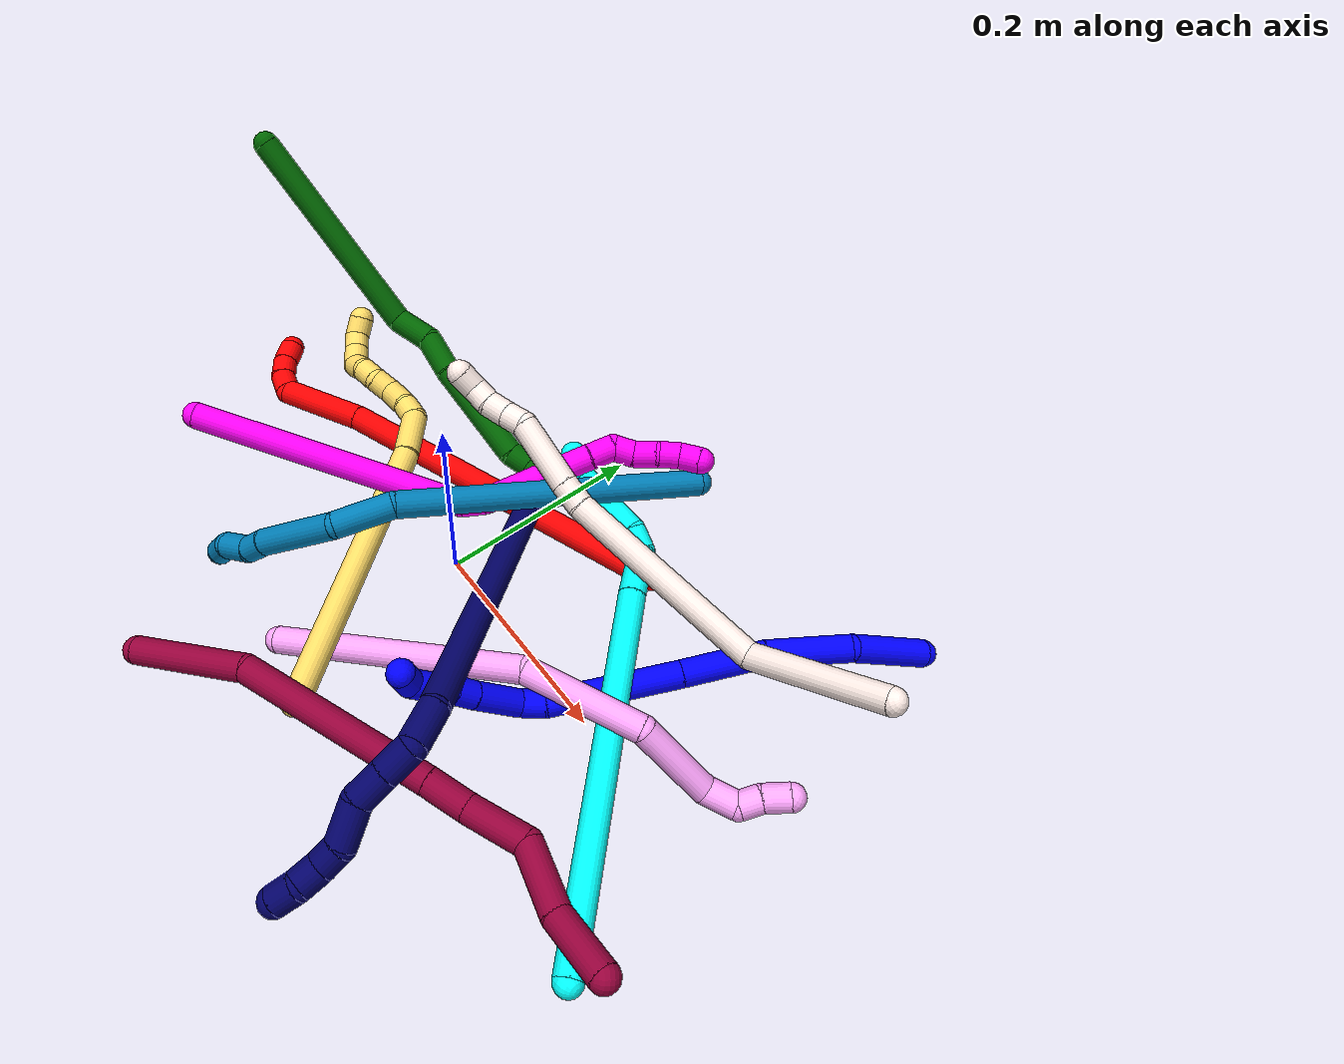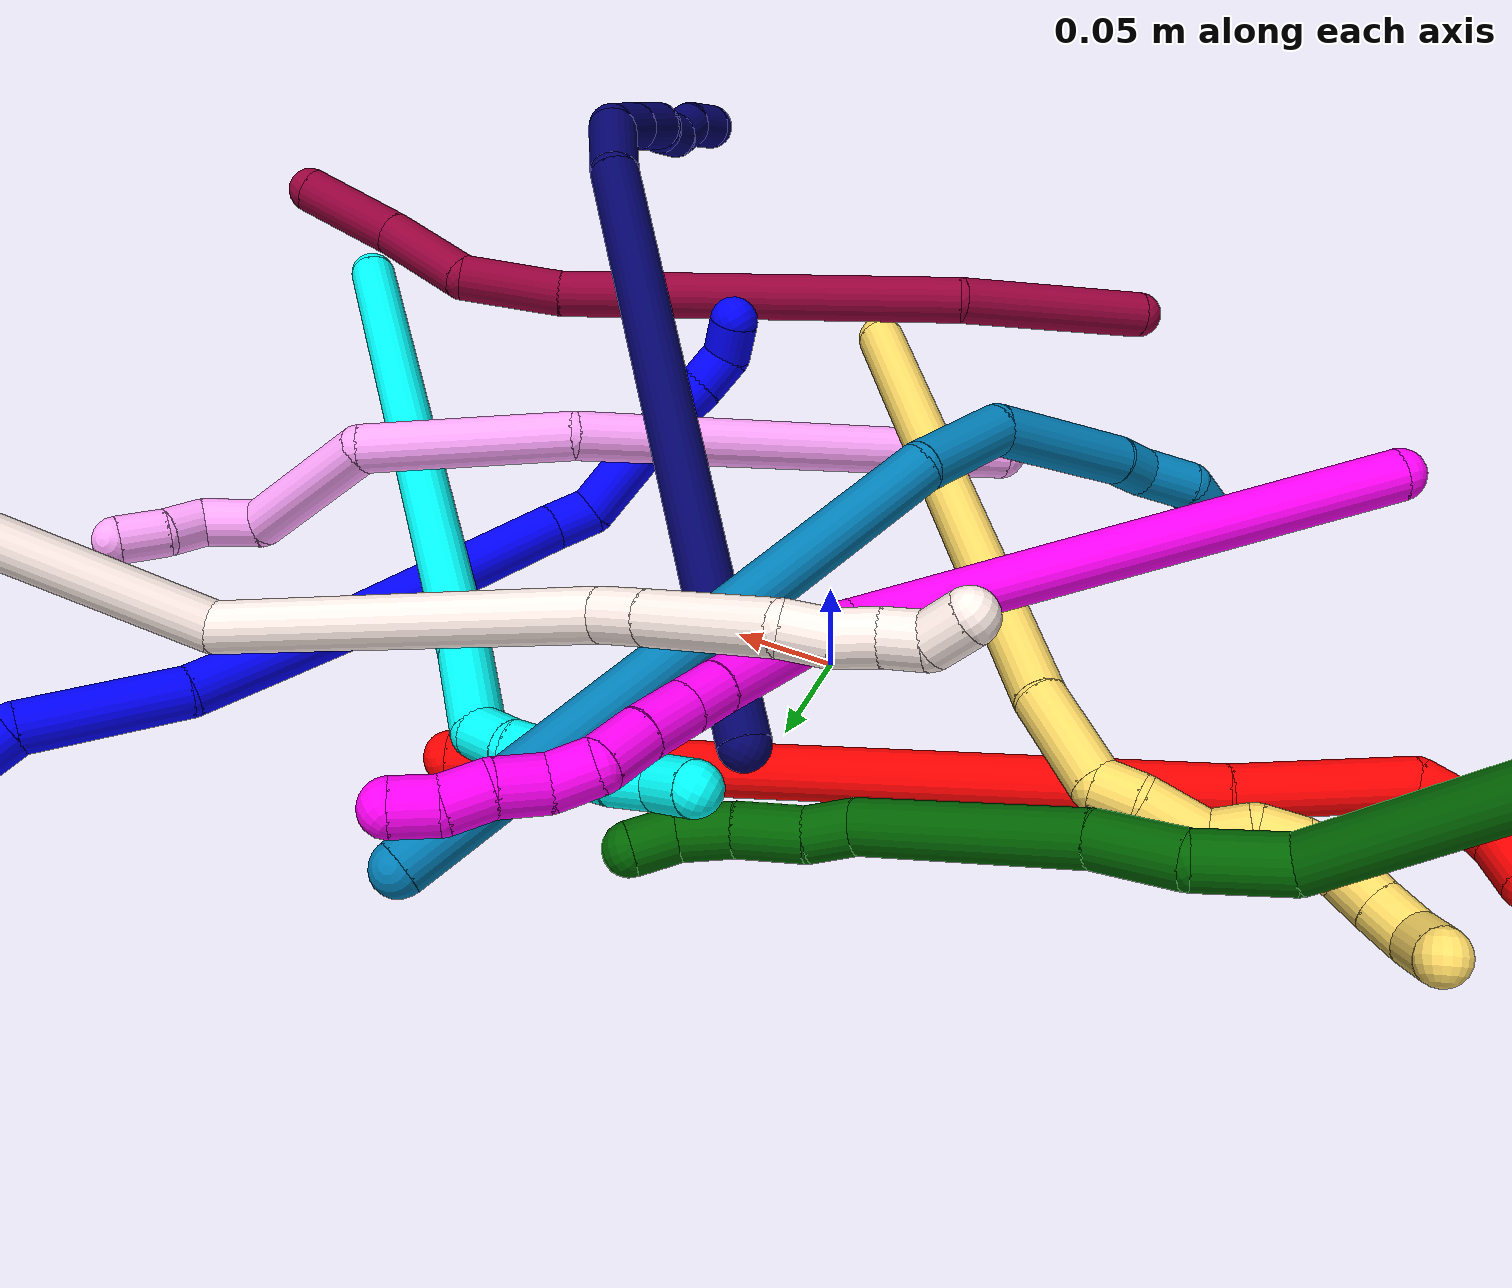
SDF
<sdf version="1.7">
 <world name="default">
  <plugin name="TubeGeneratorPlugin" filename="libtube_generator_plugin.so"/>
  <model name="photoneo_s_sensor">
   <static>1</static>
   <pose>0 0 2 1.57079 1.57079 3.14159</pose>
   <link name="link">
    <inertial><mass>0.1</mass></inertial>
    <sensor name="sensor" type="depth">
     <update_rate>30</update_rate>
     <camera>
      <horizontal_fov>1.22</horizontal_fov>
      <image><width>1920</width><height>1200</height><format>B8G8R8</format></image>
      <clip><near>0.1</near><far>4</far></clip>
      <depth_camera><output>points</output></depth_camera>
     </camera>
     <plugin name="camera_plugin" filename="libgazebo_ros_depth_camera.so">
      <baseline>0.2</baseline>
      <alwaysOn>1</alwaysOn>
      <updateRate>0.0</updateRate>
      <cameraName>camera_ir</cameraName>
      <imageTopicName>/camera/color/image_raw</imageTopicName>
      <cameraInfoTopicName>/camera/color/camera_info</cameraInfoTopicName>
      <depthImageTopicName>/camera/depth/image_raw</depthImageTopicName>
      <depthImageCameraInfoTopicName>/camera/depth/camera_info</depthImageCameraInfoTopicName>
      <pointCloudTopicName>/camera/depth/points</pointCloudTopicName>
      <frameName>fr_optical</frameName>
      <pointCloudCutoff>0.1</pointCloudCutoff>
      <pointCloudCutoffMax>2.0</pointCloudCutoffMax>
      <distortionK1>0</distortionK1>
      <distortionK2>0</distortionK2>
      <distortionK3>0</distortionK3>
      <distortionT1>0</distortionT1>
      <distortionT2>0</distortionT2>
      <CxPrime>0</CxPrime>
      <Cx>0</Cx>
      <Cy>0</Cy>
      <focalLength>0</focalLength>
      <hackBaseline>0</hackBaseline>
     </plugin>
    </sensor>
   </link>
  </model>
  <gravity>0 0 -9.8</gravity>
  <magnetic_field>6e-06 2.3e-05 -4.2e-05</magnetic_field>
  <atmosphere type="adiabatic"/>
  <physics name="default_physics" default="0" type="ode">
   <max_step_size>0.003</max_step_size>
   <real_time_factor>1</real_time_factor>
   <real_time_update_rate>1000</real_time_update_rate>
   <max_contacts>10000</max_contacts>
   <ode>
    <solver>
     <type>quick</type>
     <iters>100</iters>
     <sor>1.3</sor>
     <use_dynamic_moi_rescaling>0</use_dynamic_moi_rescaling>
    </solver>
    <constraints>
     <contact_max_correcting_vel>0</contact_max_correcting_vel>
     <contact_surface_layer>0.001</contact_surface_layer>
     <cfm>0</cfm>
     <erp>0.2</erp>
    </constraints>
   </ode>
  </physics>
  <scene><ambient>0.4 0.4 0.4 1</ambient><background>0.7 0.7 0.7 1</background><shadows>0</shadows></scene>
  <audio><device>default</device></audio>
  <spherical_coordinates>
   <surface_model>EARTH_WGS84</surface_model>
   <latitude_deg>0</latitude_deg>
   <longitude_deg>0</longitude_deg>
   <elevation>0</elevation>
   <heading_deg>0</heading_deg>
  </spherical_coordinates>
  <model name="bin">
   <static>1</static>
   <link name="bottom">
    <collision name="collision-bottom">
     <pose>0 0 -0.01 0 -0 0</pose>
     <geometry><box><size>0.8 0.6 0.02</size></box></geometry>
     <surface>
      <friction><ode><mu>100</mu><mu2>100</mu2></ode></friction>
      <contact><collide_bitmask>65535</collide_bitmask></contact>
     </surface>
    </collision>
   </link>
   <link name="west_wall">
    <collision name="collision-west_wall">
     <pose>-0.41 0 0.1 0 -0 0</pose>
     <geometry><box><size>0.02 0.6 0.2</size></box></geometry>
     <surface>
      <friction><ode><mu>100</mu><mu2>100</mu2></ode></friction>
      <contact><collide_bitmask>65535</collide_bitmask></contact>
     </surface>
    </collision>
   </link>
   <link name="east_wall">
    <collision name="collision-east_wall">
     <pose>0.41 0 0.1 0 -0 0</pose>
     <geometry><box><size>0.02 0.6 0.2</size></box></geometry>
     <surface>
      <friction><ode><mu>100</mu><mu2>100</mu2></ode></friction>
      <contact><collide_bitmask>65535</collide_bitmask></contact>
     </surface>
    </collision>
   </link>
   <link name="south_wall">
    <collision name="collision-south_wall">
     <pose>0 -0.31 0.1 0 -0 0</pose>
     <geometry><box><size>0.8 0.02 0.2</size></box></geometry>
     <surface>
      <friction><ode><mu>100</mu><mu2>100</mu2></ode></friction>
      <contact><collide_bitmask>65535</collide_bitmask></contact>
     </surface>
    </collision>
   </link>
   <link name="north_wall">
    <collision name="collision-north_wall">
     <pose>0 0.31 0.1 0 -0 0</pose>
     <geometry><box><size>0.8 0.02 0.2</size></box></geometry>
     <surface>
      <friction><ode><mu>100</mu><mu2>100</mu2></ode></friction>
      <contact><collide_bitmask>65535</collide_bitmask></contact>
     </surface>
    </collision>
   </link>
  </model>
  <model name="1">
   <static>0</static>
   <link name="1">
    <collision name="collision-cylinder-e_1_1_4">
     <pose>-0.008242 -0.035737 0.003738 1.46659 -0.225467 -0.203279</pose>
     <geometry><cylinder><radius>0.0125</radius><length>0.07373</length></cylinder></geometry>
     <surface>
      <friction><ode><mu>1.16</mu><mu2>1.16</mu2><slip1>0</slip1><slip2>0</slip2></ode></friction>
      <contact><ode><kp>1e+06</kp><kd>1</kd><max_vel>0</max_vel><min_depth>0.001</min_depth></ode></contact>
     </surface>
    </collision>
    <visual name="visual-cylinder-e_1_1_4">
     <pose>-0.008242 -0.035737 0.003738 1.46659 -0.225467 -0.203279</pose>
     <geometry><cylinder><radius>0.0125</radius><length>0.07373</length></cylinder></geometry>
     <material><ambient>0 0 1 1</ambient></material>
    </visual>
    <collision name="collision-cylinder-e_2_4_5">
     <pose>-0.01504 -0.106172 -0.005378 1.92556 0.038984 0.056006</pose>
     <geometry><cylinder><radius>0.0125</radius><length>0.07406</length></cylinder></geometry>
     <surface>
      <friction><ode><mu>1.16</mu><mu2>1.16</mu2><slip1>0</slip1><slip2>0</slip2></ode></friction>
      <contact><ode><kp>1e+06</kp><kd>1</kd><max_vel>0</max_vel><min_depth>0.001</min_depth></ode></contact>
     </surface>
    </collision>
    <visual name="visual-cylinder-e_2_4_5">
     <pose>-0.01504 -0.106172 -0.005378 1.92556 0.038984 0.056006</pose>
     <geometry><cylinder><radius>0.0125</radius><length>0.07406</length></cylinder></geometry>
     <material><ambient>0 0 1 1</ambient></material>
    </visual>
    <collision name="collision-cylinder-e_3_5_6">
     <pose>-0.007867 -0.178789 -0.02404 1.72278 0.148274 0.1726</pose>
     <geometry><cylinder><radius>0.0125</radius><length>0.077574</length></cylinder></geometry>
     <surface>
      <friction><ode><mu>1.16</mu><mu2>1.16</mu2><slip1>0</slip1><slip2>0</slip2></ode></friction>
      <contact><ode><kp>1e+06</kp><kd>1</kd><max_vel>0</max_vel><min_depth>0.001</min_depth></ode></contact>
     </surface>
    </collision>
    <visual name="visual-cylinder-e_3_5_6">
     <pose>-0.007867 -0.178789 -0.02404 1.72278 0.148274 0.1726</pose>
     <geometry><cylinder><radius>0.0125</radius><length>0.077574</length></cylinder></geometry>
     <material><ambient>0 0 1 1</ambient></material>
    </visual>
    <collision name="collision-cylinder-e_4_6_7">
     <pose>0.004844 -0.277413 -0.036292 1.67656 0.113862 0.126557</pose>
     <geometry><cylinder><radius>0.0125</radius><length>0.122888</length></cylinder></geometry>
     <surface>
      <friction><ode><mu>1.16</mu><mu2>1.16</mu2><slip1>0</slip1><slip2>0</slip2></ode></friction>
      <contact><ode><kp>1e+06</kp><kd>1</kd><max_vel>0</max_vel><min_depth>0.001</min_depth></ode></contact>
     </surface>
    </collision>
    <visual name="visual-cylinder-e_4_6_7">
     <pose>0.004844 -0.277413 -0.036292 1.67656 0.113862 0.126557</pose>
     <geometry><cylinder><radius>0.0125</radius><length>0.122888</length></cylinder></geometry>
     <material><ambient>0 0 1 1</ambient></material>
    </visual>
    <collision name="collision-cylinder-e_5_7_8">
     <pose>0.010243 -0.349324 -0.04442 1.72001 -0.138722 -0.161045</pose>
     <geometry><cylinder><radius>0.0125</radius><length>0.022884</length></cylinder></geometry>
     <surface>
      <friction><ode><mu>1.16</mu><mu2>1.16</mu2><slip1>0</slip1><slip2>0</slip2></ode></friction>
      <contact><ode><kp>1e+06</kp><kd>1</kd><max_vel>0</max_vel><min_depth>0.001</min_depth></ode></contact>
     </surface>
    </collision>
    <visual name="visual-cylinder-e_5_7_8">
     <pose>0.010243 -0.349324 -0.04442 1.72001 -0.138722 -0.161045</pose>
     <geometry><cylinder><radius>0.0125</radius><length>0.022884</length></cylinder></geometry>
     <material><ambient>0 0 1 1</ambient></material>
    </visual>
    <collision name="collision-cylinder-e_6_8_9">
     <pose>-0.000427 -0.381079 -0.038515 1.21696 -0.393267 -0.275799</pose>
     <geometry><cylinder><radius>0.0125</radius><length>0.047432</length></cylinder></geometry>
     <surface>
      <friction><ode><mu>1.16</mu><mu2>1.16</mu2><slip1>0</slip1><slip2>0</slip2></ode></friction>
      <contact><ode><kp>1e+06</kp><kd>1</kd><max_vel>0</max_vel><min_depth>0.001</min_depth></ode></contact>
     </surface>
    </collision>
    <visual name="visual-cylinder-e_6_8_9">
     <pose>-0.000427 -0.381079 -0.038515 1.21696 -0.393267 -0.275799</pose>
     <geometry><cylinder><radius>0.0125</radius><length>0.047432</length></cylinder></geometry>
     <material><ambient>0 0 1 1</ambient></material>
    </visual>
    <collision name="collision-cylinder-e_7_9_10">
     <pose>-0.013971 -0.410224 -0.028038 1.24678 -0.456718 -0.331167</pose>
     <geometry><cylinder><radius>0.0125</radius><length>0.020208</length></cylinder></geometry>
     <surface>
      <friction><ode><mu>1.16</mu><mu2>1.16</mu2><slip1>0</slip1><slip2>0</slip2></ode></friction>
      <contact><ode><kp>1e+06</kp><kd>1</kd><max_vel>0</max_vel><min_depth>0.001</min_depth></ode></contact>
     </surface>
    </collision>
    <visual name="visual-cylinder-e_7_9_10">
     <pose>-0.013971 -0.410224 -0.028038 1.24678 -0.456718 -0.331167</pose>
     <geometry><cylinder><radius>0.0125</radius><length>0.020208</length></cylinder></geometry>
     <material><ambient>0 0 1 1</ambient></material>
    </visual>
    <collision name="collision-cylinder-e_8_10_11">
     <pose>-0.021723 -0.428174 -0.02287 1.33164 -0.329809 -0.259956</pose>
     <geometry><cylinder><radius>0.0125</radius><length>0.020351</length></cylinder></geometry>
     <surface>
      <friction><ode><mu>1.16</mu><mu2>1.16</mu2><slip1>0</slip1><slip2>0</slip2></ode></friction>
      <contact><ode><kp>1e+06</kp><kd>1</kd><max_vel>0</max_vel><min_depth>0.001</min_depth></ode></contact>
     </surface>
    </collision>
    <visual name="visual-cylinder-e_8_10_11">
     <pose>-0.021723 -0.428174 -0.02287 1.33164 -0.329809 -0.259956</pose>
     <geometry><cylinder><radius>0.0125</radius><length>0.020351</length></cylinder></geometry>
     <material><ambient>0 0 1 1</ambient></material>
    </visual>
    <collision name="collision-cylinder-e_9_11_12">
     <pose>-0.02895 -0.446426 -0.017424 1.22907 -0.394469 -0.280194</pose>
     <geometry><cylinder><radius>0.0125</radius><length>0.020461</length></cylinder></geometry>
     <surface>
      <friction><ode><mu>1.16</mu><mu2>1.16</mu2><slip1>0</slip1><slip2>0</slip2></ode></friction>
      <contact><ode><kp>1e+06</kp><kd>1</kd><max_vel>0</max_vel><min_depth>0.001</min_depth></ode></contact>
     </surface>
    </collision>
    <visual name="visual-cylinder-e_9_11_12">
     <pose>-0.02895 -0.446426 -0.017424 1.22907 -0.394469 -0.280194</pose>
     <geometry><cylinder><radius>0.0125</radius><length>0.020461</length></cylinder></geometry>
     <material><ambient>0 0 1 1</ambient></material>
    </visual>
    <collision name="collision-cylinder-e_10_12_2">
     <pose>-0.039646 -0.459258 -0.007707 0.540751 -0.72453 -0.209316</pose>
     <geometry><cylinder><radius>0.0125</radius><length>0.020411</length></cylinder></geometry>
     <surface>
      <friction><ode><mu>1.16</mu><mu2>1.16</mu2><slip1>0</slip1><slip2>0</slip2></ode></friction>
      <contact><ode><kp>1e+06</kp><kd>1</kd><max_vel>0</max_vel><min_depth>0.001</min_depth></ode></contact>
     </surface>
    </collision>
    <visual name="visual-cylinder-e_10_12_2">
     <pose>-0.039646 -0.459258 -0.007707 0.540751 -0.72453 -0.209316</pose>
     <geometry><cylinder><radius>0.0125</radius><length>0.020411</length></cylinder></geometry>
     <material><ambient>0 0 1 1</ambient></material>
    </visual>
    <collision name="collision-sphere-2">
     <pose>-0.04641 -0.463192 -0.001156 0 -0 0</pose>
     <geometry><sphere><radius>0.0125</radius></sphere></geometry>
     <surface>
      <friction><ode><mu>1.16</mu><mu2>1.16</mu2><slip1>0</slip1><slip2>0</slip2></ode></friction>
      <contact><ode><kp>1e+06</kp><kd>1</kd><max_vel>0</max_vel><min_depth>0.001</min_depth></ode></contact>
     </surface>
    </collision>
    <visual name="visual-sphere-2">
     <pose>-0.04641 -0.463192 -0.001156 0 -0 0</pose>
     <geometry><sphere><radius>0.0125</radius></sphere></geometry>
     <material><ambient>0 0 1 1</ambient></material>
    </visual>
    <collision name="collision-sphere-12">
     <pose>-0.032882 -0.455324 -0.014259 0 -0 0</pose>
     <geometry><sphere><radius>0.0125</radius></sphere></geometry>
     <surface>
      <friction><ode><mu>1.16</mu><mu2>1.16</mu2><slip1>0</slip1><slip2>0</slip2></ode></friction>
      <contact><ode><kp>1e+06</kp><kd>1</kd><max_vel>0</max_vel><min_depth>0.001</min_depth></ode></contact>
     </surface>
    </collision>
    <visual name="visual-sphere-12">
     <pose>-0.032882 -0.455324 -0.014259 0 -0 0</pose>
     <geometry><sphere><radius>0.0125</radius></sphere></geometry>
     <material><ambient>0 0 1 1</ambient></material>
    </visual>
    <collision name="collision-sphere-11">
     <pose>-0.025018 -0.437527 -0.020589 0 -0 0</pose>
     <geometry><sphere><radius>0.0125</radius></sphere></geometry>
     <surface>
      <friction><ode><mu>1.16</mu><mu2>1.16</mu2><slip1>0</slip1><slip2>0</slip2></ode></friction>
      <contact><ode><kp>1e+06</kp><kd>1</kd><max_vel>0</max_vel><min_depth>0.001</min_depth></ode></contact>
     </surface>
    </collision>
    <visual name="visual-sphere-11">
     <pose>-0.025018 -0.437527 -0.020589 0 -0 0</pose>
     <geometry><sphere><radius>0.0125</radius></sphere></geometry>
     <material><ambient>0 0 1 1</ambient></material>
    </visual>
    <collision name="collision-sphere-10">
     <pose>-0.018427 -0.41882 -0.02515 0 -0 0</pose>
     <geometry><sphere><radius>0.0125</radius></sphere></geometry>
     <surface>
      <friction><ode><mu>1.16</mu><mu2>1.16</mu2><slip1>0</slip1><slip2>0</slip2></ode></friction>
      <contact><ode><kp>1e+06</kp><kd>1</kd><max_vel>0</max_vel><min_depth>0.001</min_depth></ode></contact>
     </surface>
    </collision>
    <visual name="visual-sphere-10">
     <pose>-0.018427 -0.41882 -0.02515 0 -0 0</pose>
     <geometry><sphere><radius>0.0125</radius></sphere></geometry>
     <material><ambient>0 0 1 1</ambient></material>
    </visual>
    <collision name="collision-sphere-9">
     <pose>-0.009515 -0.401628 -0.030925 0 -0 0</pose>
     <geometry><sphere><radius>0.0125</radius></sphere></geometry>
     <surface>
      <friction><ode><mu>1.16</mu><mu2>1.16</mu2><slip1>0</slip1><slip2>0</slip2></ode></friction>
      <contact><ode><kp>1e+06</kp><kd>1</kd><max_vel>0</max_vel><min_depth>0.001</min_depth></ode></contact>
     </surface>
    </collision>
    <visual name="visual-sphere-9">
     <pose>-0.009515 -0.401628 -0.030925 0 -0 0</pose>
     <geometry><sphere><radius>0.0125</radius></sphere></geometry>
     <material><ambient>0 0 1 1</ambient></material>
    </visual>
    <collision name="collision-sphere-4">
     <pose>-0.016483 -0.071474 0.007475 0 -0 0</pose>
     <geometry><sphere><radius>0.0125</radius></sphere></geometry>
     <surface>
      <friction><ode><mu>1.16</mu><mu2>1.16</mu2><slip1>0</slip1><slip2>0</slip2></ode></friction>
      <contact><ode><kp>1e+06</kp><kd>1</kd><max_vel>0</max_vel><min_depth>0.001</min_depth></ode></contact>
     </surface>
    </collision>
    <visual name="visual-sphere-4">
     <pose>-0.016483 -0.071474 0.007475 0 -0 0</pose>
     <geometry><sphere><radius>0.0125</radius></sphere></geometry>
     <material><ambient>0 0 1 1</ambient></material>
    </visual>
    <collision name="collision-sphere-1">
     <geometry><sphere><radius>0.0125</radius></sphere></geometry>
     <surface>
      <friction><ode><mu>1.16</mu><mu2>1.16</mu2><slip1>0</slip1><slip2>0</slip2></ode></friction>
      <contact><ode><kp>1e+06</kp><kd>1</kd><max_vel>0</max_vel><min_depth>0.001</min_depth></ode></contact>
     </surface>
    </collision>
    <visual name="visual-sphere-1">
     <geometry><sphere><radius>0.0125</radius></sphere></geometry>
     <material><ambient>0 0 1 1</ambient></material>
    </visual>
    <collision name="collision-sphere-8">
     <pose>0.008661 -0.36053 -0.046105 0 -0 0</pose>
     <geometry><sphere><radius>0.0125</radius></sphere></geometry>
     <surface>
      <friction><ode><mu>1.16</mu><mu2>1.16</mu2><slip1>0</slip1><slip2>0</slip2></ode></friction>
      <contact><ode><kp>1e+06</kp><kd>1</kd><max_vel>0</max_vel><min_depth>0.001</min_depth></ode></contact>
     </surface>
    </collision>
    <visual name="visual-sphere-8">
     <pose>0.008661 -0.36053 -0.046105 0 -0 0</pose>
     <geometry><sphere><radius>0.0125</radius></sphere></geometry>
     <material><ambient>0 0 1 1</ambient></material>
    </visual>
    <collision name="collision-sphere-5">
     <pose>-0.013597 -0.14087 -0.018232 0 -0 0</pose>
     <geometry><sphere><radius>0.0125</radius></sphere></geometry>
     <surface>
      <friction><ode><mu>1.16</mu><mu2>1.16</mu2><slip1>0</slip1><slip2>0</slip2></ode></friction>
      <contact><ode><kp>1e+06</kp><kd>1</kd><max_vel>0</max_vel><min_depth>0.001</min_depth></ode></contact>
     </surface>
    </collision>
    <visual name="visual-sphere-5">
     <pose>-0.013597 -0.14087 -0.018232 0 -0 0</pose>
     <geometry><sphere><radius>0.0125</radius></sphere></geometry>
     <material><ambient>0 0 1 1</ambient></material>
    </visual>
    <collision name="collision-sphere-6">
     <pose>-0.002137 -0.216708 -0.029847 0 -0 0</pose>
     <geometry><sphere><radius>0.0125</radius></sphere></geometry>
     <surface>
      <friction><ode><mu>1.16</mu><mu2>1.16</mu2><slip1>0</slip1><slip2>0</slip2></ode></friction>
      <contact><ode><kp>1e+06</kp><kd>1</kd><max_vel>0</max_vel><min_depth>0.001</min_depth></ode></contact>
     </surface>
    </collision>
    <visual name="visual-sphere-6">
     <pose>-0.002137 -0.216708 -0.029847 0 -0 0</pose>
     <geometry><sphere><radius>0.0125</radius></sphere></geometry>
     <material><ambient>0 0 1 1</ambient></material>
    </visual>
    <collision name="collision-sphere-7">
     <pose>0.011825 -0.338118 -0.042736 0 -0 0</pose>
     <geometry><sphere><radius>0.0125</radius></sphere></geometry>
     <surface>
      <friction><ode><mu>1.16</mu><mu2>1.16</mu2><slip1>0</slip1><slip2>0</slip2></ode></friction>
      <contact><ode><kp>1e+06</kp><kd>1</kd><max_vel>0</max_vel><min_depth>0.001</min_depth></ode></contact>
     </surface>
    </collision>
    <visual name="visual-sphere-7">
     <pose>0.011825 -0.338118 -0.042736 0 -0 0</pose>
     <geometry><sphere><radius>0.0125</radius></sphere></geometry>
     <material><ambient>0 0 1 1</ambient></material>
    </visual>
    <inertial>
     <pose>-0.007297 -0.240079 -0.021673 0 -0 0</pose>
     <mass>0.5</mass>
     <inertia><ixx>0.0003</ixx><ixy>0</ixy><ixz>0</ixz><iyy>-3.8e-05</iyy><iyz>0</iyz><izz>0.000273</izz></inertia>
    </inertial>
   </link>
   <pose>0.329177 0.281481 0.011495 -0.159529 0.772453 -0.532673</pose>
  </model>
  <model name="2">
   <static>0</static>
   <link name="2">
    <collision name="collision-cylinder-e_1_1_4">
     <pose>-0.142229 -0.062531 0.079883 0.664155 -0.951224 -0.351559</pose>
     <geometry><cylinder><radius>0.0125</radius><length>0.349402</length></cylinder></geometry>
     <surface>
      <friction><ode><mu>1.16</mu><mu2>1.16</mu2><slip1>0</slip1><slip2>0</slip2></ode></friction>
      <contact><ode><kp>1e+06</kp><kd>1</kd><max_vel>0</max_vel><min_depth>0.001</min_depth></ode></contact>
     </surface>
    </collision>
    <visual name="visual-cylinder-e_1_1_4">
     <pose>-0.142229 -0.062531 0.079883 0.664155 -0.951224 -0.351559</pose>
     <geometry><cylinder><radius>0.0125</radius><length>0.349402</length></cylinder></geometry>
     <material><ambient>1 0 0 1</ambient></material>
    </visual>
    <collision name="collision-cylinder-e_2_4_5">
     <pose>-0.320428 -0.134762 0.180666 0.434504 -1.00108 -0.240324</pose>
     <geometry><cylinder><radius>0.0125</radius><length>0.085435</length></cylinder></geometry>
     <surface>
      <friction><ode><mu>1.16</mu><mu2>1.16</mu2><slip1>0</slip1><slip2>0</slip2></ode></friction>
      <contact><ode><kp>1e+06</kp><kd>1</kd><max_vel>0</max_vel><min_depth>0.001</min_depth></ode></contact>
     </surface>
    </collision>
    <visual name="visual-cylinder-e_2_4_5">
     <pose>-0.320428 -0.134762 0.180666 0.434504 -1.00108 -0.240324</pose>
     <geometry><cylinder><radius>0.0125</radius><length>0.085435</length></cylinder></geometry>
     <material><ambient>1 0 0 1</ambient></material>
    </visual>
    <collision name="collision-cylinder-e_3_5_6">
     <pose>-0.361184 -0.153734 0.205422 1.17678 -0.444729 -0.299467</pose>
     <geometry><cylinder><radius>0.0125</radius><length>0.02225</length></cylinder></geometry>
     <surface>
      <friction><ode><mu>1.16</mu><mu2>1.16</mu2><slip1>0</slip1><slip2>0</slip2></ode></friction>
      <contact><ode><kp>1e+06</kp><kd>1</kd><max_vel>0</max_vel><min_depth>0.001</min_depth></ode></contact>
     </surface>
    </collision>
    <visual name="visual-cylinder-e_3_5_6">
     <pose>-0.361184 -0.153734 0.205422 1.17678 -0.444729 -0.299467</pose>
     <geometry><cylinder><radius>0.0125</radius><length>0.02225</length></cylinder></geometry>
     <material><ambient>1 0 0 1</ambient></material>
    </visual>
    <collision name="collision-cylinder-e_4_6_7">
     <pose>-0.367724 -0.173132 0.211316 1.37211 -0.168213 -0.137828</pose>
     <geometry><cylinder><radius>0.0125</radius><length>0.020951</length></cylinder></geometry>
     <surface>
      <friction><ode><mu>1.16</mu><mu2>1.16</mu2><slip1>0</slip1><slip2>0</slip2></ode></friction>
      <contact><ode><kp>1e+06</kp><kd>1</kd><max_vel>0</max_vel><min_depth>0.001</min_depth></ode></contact>
     </surface>
    </collision>
    <visual name="visual-cylinder-e_4_6_7">
     <pose>-0.367724 -0.173132 0.211316 1.37211 -0.168213 -0.137828</pose>
     <geometry><cylinder><radius>0.0125</radius><length>0.020951</length></cylinder></geometry>
     <material><ambient>1 0 0 1</ambient></material>
    </visual>
    <collision name="collision-cylinder-e_5_7_2">
     <pose>-0.368987 -0.194196 0.214179 1.4955 0.044721 0.041476</pose>
     <geometry><cylinder><radius>0.0125</radius><length>0.021962</length></cylinder></geometry>
     <surface>
      <friction><ode><mu>1.16</mu><mu2>1.16</mu2><slip1>0</slip1><slip2>0</slip2></ode></friction>
      <contact><ode><kp>1e+06</kp><kd>1</kd><max_vel>0</max_vel><min_depth>0.001</min_depth></ode></contact>
     </surface>
    </collision>
    <visual name="visual-cylinder-e_5_7_2">
     <pose>-0.368987 -0.194196 0.214179 1.4955 0.044721 0.041476</pose>
     <geometry><cylinder><radius>0.0125</radius><length>0.021962</length></cylinder></geometry>
     <material><ambient>1 0 0 1</ambient></material>
    </visual>
    <collision name="collision-sphere-2">
     <pose>-0.368496 -0.205135 0.215005 0 -0 0</pose>
     <geometry><sphere><radius>0.0125</radius></sphere></geometry>
     <surface>
      <friction><ode><mu>1.16</mu><mu2>1.16</mu2><slip1>0</slip1><slip2>0</slip2></ode></friction>
      <contact><ode><kp>1e+06</kp><kd>1</kd><max_vel>0</max_vel><min_depth>0.001</min_depth></ode></contact>
     </surface>
    </collision>
    <visual name="visual-sphere-2">
     <pose>-0.368496 -0.205135 0.215005 0 -0 0</pose>
     <geometry><sphere><radius>0.0125</radius></sphere></geometry>
     <material><ambient>1 0 0 1</ambient></material>
    </visual>
    <collision name="collision-sphere-7">
     <pose>-0.369478 -0.183257 0.213354 0 -0 0</pose>
     <geometry><sphere><radius>0.0125</radius></sphere></geometry>
     <surface>
      <friction><ode><mu>1.16</mu><mu2>1.16</mu2><slip1>0</slip1><slip2>0</slip2></ode></friction>
      <contact><ode><kp>1e+06</kp><kd>1</kd><max_vel>0</max_vel><min_depth>0.001</min_depth></ode></contact>
     </surface>
    </collision>
    <visual name="visual-sphere-7">
     <pose>-0.369478 -0.183257 0.213354 0 -0 0</pose>
     <geometry><sphere><radius>0.0125</radius></sphere></geometry>
     <material><ambient>1 0 0 1</ambient></material>
    </visual>
    <collision name="collision-sphere-6">
     <pose>-0.365971 -0.163008 0.209277 0 -0 0</pose>
     <geometry><sphere><radius>0.0125</radius></sphere></geometry>
     <surface>
      <friction><ode><mu>1.16</mu><mu2>1.16</mu2><slip1>0</slip1><slip2>0</slip2></ode></friction>
      <contact><ode><kp>1e+06</kp><kd>1</kd><max_vel>0</max_vel><min_depth>0.001</min_depth></ode></contact>
     </surface>
    </collision>
    <visual name="visual-sphere-6">
     <pose>-0.365971 -0.163008 0.209277 0 -0 0</pose>
     <geometry><sphere><radius>0.0125</radius></sphere></geometry>
     <material><ambient>1 0 0 1</ambient></material>
    </visual>
    <collision name="collision-sphere-5">
     <pose>-0.356398 -0.144461 0.201567 0 -0 0</pose>
     <geometry><sphere><radius>0.0125</radius></sphere></geometry>
     <surface>
      <friction><ode><mu>1.16</mu><mu2>1.16</mu2><slip1>0</slip1><slip2>0</slip2></ode></friction>
      <contact><ode><kp>1e+06</kp><kd>1</kd><max_vel>0</max_vel><min_depth>0.001</min_depth></ode></contact>
     </surface>
    </collision>
    <visual name="visual-sphere-5">
     <pose>-0.356398 -0.144461 0.201567 0 -0 0</pose>
     <geometry><sphere><radius>0.0125</radius></sphere></geometry>
     <material><ambient>1 0 0 1</ambient></material>
    </visual>
    <collision name="collision-sphere-1">
     <geometry><sphere><radius>0.0125</radius></sphere></geometry>
     <surface>
      <friction><ode><mu>1.16</mu><mu2>1.16</mu2><slip1>0</slip1><slip2>0</slip2></ode></friction>
      <contact><ode><kp>1e+06</kp><kd>1</kd><max_vel>0</max_vel><min_depth>0.001</min_depth></ode></contact>
     </surface>
    </collision>
    <visual name="visual-sphere-1">
     <geometry><sphere><radius>0.0125</radius></sphere></geometry>
     <material><ambient>1 0 0 1</ambient></material>
    </visual>
    <collision name="collision-sphere-4">
     <pose>-0.284457 -0.125062 0.159766 0 -0 0</pose>
     <geometry><sphere><radius>0.0125</radius></sphere></geometry>
     <surface>
      <friction><ode><mu>1.16</mu><mu2>1.16</mu2><slip1>0</slip1><slip2>0</slip2></ode></friction>
      <contact><ode><kp>1e+06</kp><kd>1</kd><max_vel>0</max_vel><min_depth>0.001</min_depth></ode></contact>
     </surface>
    </collision>
    <visual name="visual-sphere-4">
     <pose>-0.284457 -0.125062 0.159766 0 -0 0</pose>
     <geometry><sphere><radius>0.0125</radius></sphere></geometry>
     <material><ambient>1 0 0 1</ambient></material>
    </visual>
    <inertial>
     <pose>-0.20183 -0.089349 0.114096 0 -0 0</pose>
     <mass>0.5</mass>
     <inertia>
      <ixx>0.001229</ixx>
      <ixy>0</ixy>
      <ixz>0</ixz>
      <iyy>0.002572</iyy>
      <iyz>0</iyz>
      <izz>0.004264</izz>
     </inertia>
    </inertial>
   </link>
   <pose>0.126584 0.136921 0.011489 -3.05653 0.492781 0.773168</pose>
  </model>
  <model name="3">
   <static>0</static>
   <link name="3">
    <collision name="collision-cylinder-e_1_1_4">
     <pose>-0.087101 0.102652 -0.097759 -2.33179 -0.550975 1.16612</pose>
     <geometry><cylinder><radius>0.0125</radius><length>0.332751</length></cylinder></geometry>
     <surface>
      <friction><ode><mu>1.16</mu><mu2>1.16</mu2><slip1>0</slip1><slip2>0</slip2></ode></friction>
      <contact><ode><kp>1e+06</kp><kd>1</kd><max_vel>0</max_vel><min_depth>0.001</min_depth></ode></contact>
     </surface>
    </collision>
    <visual name="visual-cylinder-e_1_1_4">
     <pose>-0.087101 0.102652 -0.097759 -2.33179 -0.550975 1.16612</pose>
     <geometry><cylinder><radius>0.0125</radius><length>0.332751</length></cylinder></geometry>
     <material><ambient>0.003922 1 0.996078 1</ambient></material>
    </visual>
    <collision name="collision-cylinder-e_2_4_5">
     <pose>-0.186663 0.221406 -0.209261 -2.27731 -0.532048 1.06724</pose>
     <geometry><cylinder><radius>0.0125</radius><length>0.04913</length></cylinder></geometry>
     <surface>
      <friction><ode><mu>1.16</mu><mu2>1.16</mu2><slip1>0</slip1><slip2>0</slip2></ode></friction>
      <contact><ode><kp>1e+06</kp><kd>1</kd><max_vel>0</max_vel><min_depth>0.001</min_depth></ode></contact>
     </surface>
    </collision>
    <visual name="visual-cylinder-e_2_4_5">
     <pose>-0.186663 0.221406 -0.209261 -2.27731 -0.532048 1.06724</pose>
     <geometry><cylinder><radius>0.0125</radius><length>0.04913</length></cylinder></geometry>
     <material><ambient>0.003922 1 0.996078 1</ambient></material>
    </visual>
    <collision name="collision-cylinder-e_3_5_6">
     <pose>-0.205966 0.237972 -0.231606 -3.0877 -0.671167 2.98735</pose>
     <geometry><cylinder><radius>0.0125</radius><length>0.022001</length></cylinder></geometry>
     <surface>
      <friction><ode><mu>1.16</mu><mu2>1.16</mu2><slip1>0</slip1><slip2>0</slip2></ode></friction>
      <contact><ode><kp>1e+06</kp><kd>1</kd><max_vel>0</max_vel><min_depth>0.001</min_depth></ode></contact>
     </surface>
    </collision>
    <visual name="visual-cylinder-e_3_5_6">
     <pose>-0.205966 0.237972 -0.231606 -3.0877 -0.671167 2.98735</pose>
     <geometry><cylinder><radius>0.0125</radius><length>0.022001</length></cylinder></geometry>
     <material><ambient>0.003922 1 0.996078 1</ambient></material>
    </visual>
    <collision name="collision-cylinder-e_4_6_7">
     <pose>-0.221868 0.235346 -0.26346 3.00945 -0.368645 -2.45952</pose>
     <geometry><cylinder><radius>0.0125</radius><length>0.050291</length></cylinder></geometry>
     <surface>
      <friction><ode><mu>1.16</mu><mu2>1.16</mu2><slip1>0</slip1><slip2>0</slip2></ode></friction>
      <contact><ode><kp>1e+06</kp><kd>1</kd><max_vel>0</max_vel><min_depth>0.001</min_depth></ode></contact>
     </surface>
    </collision>
    <visual name="visual-cylinder-e_4_6_7">
     <pose>-0.221868 0.235346 -0.26346 3.00945 -0.368645 -2.45952</pose>
     <geometry><cylinder><radius>0.0125</radius><length>0.050291</length></cylinder></geometry>
     <material><ambient>0.003922 1 0.996078 1</ambient></material>
    </visual>
    <collision name="collision-cylinder-e_5_7_8">
     <pose>-0.236743 0.229522 -0.296032 2.85633 -0.539258 -2.18312</pose>
     <geometry><cylinder><radius>0.0125</radius><length>0.022641</length></cylinder></geometry>
     <surface>
      <friction><ode><mu>1.16</mu><mu2>1.16</mu2><slip1>0</slip1><slip2>0</slip2></ode></friction>
      <contact><ode><kp>1e+06</kp><kd>1</kd><max_vel>0</max_vel><min_depth>0.001</min_depth></ode></contact>
     </surface>
    </collision>
    <visual name="visual-cylinder-e_5_7_8">
     <pose>-0.236743 0.229522 -0.296032 2.85633 -0.539258 -2.18312</pose>
     <geometry><cylinder><radius>0.0125</radius><length>0.022641</length></cylinder></geometry>
     <material><ambient>0.003922 1 0.996078 1</ambient></material>
    </visual>
    <collision name="collision-cylinder-e_6_8_2">
     <pose>-0.251306 0.22574 -0.312886 3.00333 -0.855313 -2.84006</pose>
     <geometry><cylinder><radius>0.0125</radius><length>0.023186</length></cylinder></geometry>
     <surface>
      <friction><ode><mu>1.16</mu><mu2>1.16</mu2><slip1>0</slip1><slip2>0</slip2></ode></friction>
      <contact><ode><kp>1e+06</kp><kd>1</kd><max_vel>0</max_vel><min_depth>0.001</min_depth></ode></contact>
     </surface>
    </collision>
    <visual name="visual-cylinder-e_6_8_2">
     <pose>-0.251306 0.22574 -0.312886 3.00333 -0.855313 -2.84006</pose>
     <geometry><cylinder><radius>0.0125</radius><length>0.023186</length></cylinder></geometry>
     <material><ambient>0.003922 1 0.996078 1</ambient></material>
    </visual>
    <collision name="collision-sphere-2">
     <pose>-0.260056 0.224692 -0.320418 0 -0 0</pose>
     <geometry><sphere><radius>0.0125</radius></sphere></geometry>
     <surface>
      <friction><ode><mu>1.16</mu><mu2>1.16</mu2><slip1>0</slip1><slip2>0</slip2></ode></friction>
      <contact><ode><kp>1e+06</kp><kd>1</kd><max_vel>0</max_vel><min_depth>0.001</min_depth></ode></contact>
     </surface>
    </collision>
    <visual name="visual-sphere-2">
     <pose>-0.260056 0.224692 -0.320418 0 -0 0</pose>
     <geometry><sphere><radius>0.0125</radius></sphere></geometry>
     <material><ambient>0.003922 1 0.996078 1</ambient></material>
    </visual>
    <collision name="collision-sphere-4">
     <pose>-0.174201 0.205304 -0.195519 0 -0 0</pose>
     <geometry><sphere><radius>0.0125</radius></sphere></geometry>
     <surface>
      <friction><ode><mu>1.16</mu><mu2>1.16</mu2><slip1>0</slip1><slip2>0</slip2></ode></friction>
      <contact><ode><kp>1e+06</kp><kd>1</kd><max_vel>0</max_vel><min_depth>0.001</min_depth></ode></contact>
     </surface>
    </collision>
    <visual name="visual-sphere-4">
     <pose>-0.174201 0.205304 -0.195519 0 -0 0</pose>
     <geometry><sphere><radius>0.0125</radius></sphere></geometry>
     <material><ambient>0.003922 1 0.996078 1</ambient></material>
    </visual>
    <collision name="collision-sphere-1">
     <geometry><sphere><radius>0.0125</radius></sphere></geometry>
     <surface>
      <friction><ode><mu>1.16</mu><mu2>1.16</mu2><slip1>0</slip1><slip2>0</slip2></ode></friction>
      <contact><ode><kp>1e+06</kp><kd>1</kd><max_vel>0</max_vel><min_depth>0.001</min_depth></ode></contact>
     </surface>
    </collision>
    <visual name="visual-sphere-1">
     <geometry><sphere><radius>0.0125</radius></sphere></geometry>
     <material><ambient>0.003922 1 0.996078 1</ambient></material>
    </visual>
    <collision name="collision-sphere-8">
     <pose>-0.242556 0.226788 -0.305354 0 -0 0</pose>
     <geometry><sphere><radius>0.0125</radius></sphere></geometry>
     <surface>
      <friction><ode><mu>1.16</mu><mu2>1.16</mu2><slip1>0</slip1><slip2>0</slip2></ode></friction>
      <contact><ode><kp>1e+06</kp><kd>1</kd><max_vel>0</max_vel><min_depth>0.001</min_depth></ode></contact>
     </surface>
    </collision>
    <visual name="visual-sphere-8">
     <pose>-0.242556 0.226788 -0.305354 0 -0 0</pose>
     <geometry><sphere><radius>0.0125</radius></sphere></geometry>
     <material><ambient>0.003922 1 0.996078 1</ambient></material>
    </visual>
    <collision name="collision-sphere-5">
     <pose>-0.199125 0.237508 -0.223004 0 -0 0</pose>
     <geometry><sphere><radius>0.0125</radius></sphere></geometry>
     <surface>
      <friction><ode><mu>1.16</mu><mu2>1.16</mu2><slip1>0</slip1><slip2>0</slip2></ode></friction>
      <contact><ode><kp>1e+06</kp><kd>1</kd><max_vel>0</max_vel><min_depth>0.001</min_depth></ode></contact>
     </surface>
    </collision>
    <visual name="visual-sphere-5">
     <pose>-0.199125 0.237508 -0.223004 0 -0 0</pose>
     <geometry><sphere><radius>0.0125</radius></sphere></geometry>
     <material><ambient>0.003922 1 0.996078 1</ambient></material>
    </visual>
    <collision name="collision-sphere-6">
     <pose>-0.212807 0.238436 -0.240208 0 -0 0</pose>
     <geometry><sphere><radius>0.0125</radius></sphere></geometry>
     <surface>
      <friction><ode><mu>1.16</mu><mu2>1.16</mu2><slip1>0</slip1><slip2>0</slip2></ode></friction>
      <contact><ode><kp>1e+06</kp><kd>1</kd><max_vel>0</max_vel><min_depth>0.001</min_depth></ode></contact>
     </surface>
    </collision>
    <visual name="visual-sphere-6">
     <pose>-0.212807 0.238436 -0.240208 0 -0 0</pose>
     <geometry><sphere><radius>0.0125</radius></sphere></geometry>
     <material><ambient>0.003922 1 0.996078 1</ambient></material>
    </visual>
    <collision name="collision-sphere-7">
     <pose>-0.23093 0.232255 -0.286711 0 -0 0</pose>
     <geometry><sphere><radius>0.0125</radius></sphere></geometry>
     <surface>
      <friction><ode><mu>1.16</mu><mu2>1.16</mu2><slip1>0</slip1><slip2>0</slip2></ode></friction>
      <contact><ode><kp>1e+06</kp><kd>1</kd><max_vel>0</max_vel><min_depth>0.001</min_depth></ode></contact>
     </surface>
    </collision>
    <visual name="visual-sphere-7">
     <pose>-0.23093 0.232255 -0.286711 0 -0 0</pose>
     <geometry><sphere><radius>0.0125</radius></sphere></geometry>
     <material><ambient>0.003922 1 0.996078 1</ambient></material>
    </visual>
    <inertial>
     <pose>-0.13006 0.145075 -0.150225 0 -0 0</pose>
     <mass>0.5</mass>
     <inertia>
      <ixx>0.003421</ixx>
      <ixy>0</ixy>
      <ixz>0</ixz>
      <iyy>0.002685</iyy>
      <iyz>0</iyz>
      <izz>-0.000305</izz>
     </inertia>
    </inertial>
   </link>
   <pose>0.367695 -0.144437 0.043329 -0.88158 1.00064 -0.879888</pose>
  </model>
  <model name="4">
   <static>0</static>
   <link name="4">
    <collision name="collision-cylinder-e_1_1_4">
     <pose>0.099212 0.010861 -0.063949 -2.97336 0.991753 -2.83236</pose>
     <geometry><cylinder><radius>0.0125</radius><length>0.237069</length></cylinder></geometry>
     <surface>
      <friction><ode><mu>1.16</mu><mu2>1.16</mu2><slip1>0</slip1><slip2>0</slip2></ode></friction>
      <contact><ode><kp>1e+06</kp><kd>1</kd><max_vel>0</max_vel><min_depth>0.001</min_depth></ode></contact>
     </surface>
    </collision>
    <visual name="visual-cylinder-e_1_1_4">
     <pose>0.099212 0.010861 -0.063949 -2.97336 0.991753 -2.83236</pose>
     <geometry><cylinder><radius>0.0125</radius><length>0.237069</length></cylinder></geometry>
     <material><ambient>1 0.65098 0.996078 1</ambient></material>
    </visual>
    <collision name="collision-cylinder-e_2_4_5">
     <pose>0.251607 0.02347 -0.138797 -2.98252 1.36615 -2.94632</pose>
     <geometry><cylinder><radius>0.0125</radius><length>0.108634</length></cylinder></geometry>
     <surface>
      <friction><ode><mu>1.16</mu><mu2>1.16</mu2><slip1>0</slip1><slip2>0</slip2></ode></friction>
      <contact><ode><kp>1e+06</kp><kd>1</kd><max_vel>0</max_vel><min_depth>0.001</min_depth></ode></contact>
     </surface>
    </collision>
    <visual name="visual-cylinder-e_2_4_5">
     <pose>0.251607 0.02347 -0.138797 -2.98252 1.36615 -2.94632</pose>
     <geometry><cylinder><radius>0.0125</radius><length>0.108634</length></cylinder></geometry>
     <material><ambient>1 0.65098 0.996078 1</ambient></material>
    </visual>
    <collision name="collision-cylinder-e_3_5_6">
     <pose>0.340381 0.010427 -0.13923 0.95499 1.09987 0.614307</pose>
     <geometry><cylinder><radius>0.0125</radius><length>0.079876</length></cylinder></geometry>
     <surface>
      <friction><ode><mu>1.16</mu><mu2>1.16</mu2><slip1>0</slip1><slip2>0</slip2></ode></friction>
      <contact><ode><kp>1e+06</kp><kd>1</kd><max_vel>0</max_vel><min_depth>0.001</min_depth></ode></contact>
     </surface>
    </collision>
    <visual name="visual-cylinder-e_3_5_6">
     <pose>0.340381 0.010427 -0.13923 0.95499 1.09987 0.614307</pose>
     <geometry><cylinder><radius>0.0125</radius><length>0.079876</length></cylinder></geometry>
     <material><ambient>1 0.65098 0.996078 1</ambient></material>
    </visual>
    <collision name="collision-cylinder-e_4_6_7">
     <pose>0.390406 -0.002761 -0.132452 -2.73156 1.29901 -2.60707</pose>
     <geometry><cylinder><radius>0.0125</radius><length>0.029971</length></cylinder></geometry>
     <surface>
      <friction><ode><mu>1.16</mu><mu2>1.16</mu2><slip1>0</slip1><slip2>0</slip2></ode></friction>
      <contact><ode><kp>1e+06</kp><kd>1</kd><max_vel>0</max_vel><min_depth>0.001</min_depth></ode></contact>
     </surface>
    </collision>
    <visual name="visual-cylinder-e_4_6_7">
     <pose>0.390406 -0.002761 -0.132452 -2.73156 1.29901 -2.60707</pose>
     <geometry><cylinder><radius>0.0125</radius><length>0.029971</length></cylinder></geometry>
     <material><ambient>1 0.65098 0.996078 1</ambient></material>
    </visual>
    <collision name="collision-cylinder-e_5_7_8">
     <pose>0.410682 -0.003565 -0.144024 2.84518 0.616446 2.26458</pose>
     <geometry><cylinder><radius>0.0125</radius><length>0.020203</length></cylinder></geometry>
     <surface>
      <friction><ode><mu>1.16</mu><mu2>1.16</mu2><slip1>0</slip1><slip2>0</slip2></ode></friction>
      <contact><ode><kp>1e+06</kp><kd>1</kd><max_vel>0</max_vel><min_depth>0.001</min_depth></ode></contact>
     </surface>
    </collision>
    <visual name="visual-cylinder-e_5_7_8">
     <pose>0.410682 -0.003565 -0.144024 2.84518 0.616446 2.26458</pose>
     <geometry><cylinder><radius>0.0125</radius><length>0.020203</length></cylinder></geometry>
     <material><ambient>1 0.65098 0.996078 1</ambient></material>
    </visual>
    <collision name="collision-cylinder-e_6_8_2">
     <pose>0.425761 -0.007337 -0.159639 2.96691 0.866453 2.76738</pose>
     <geometry><cylinder><radius>0.0125</radius><length>0.024248</length></cylinder></geometry>
     <surface>
      <friction><ode><mu>1.16</mu><mu2>1.16</mu2><slip1>0</slip1><slip2>0</slip2></ode></friction>
      <contact><ode><kp>1e+06</kp><kd>1</kd><max_vel>0</max_vel><min_depth>0.001</min_depth></ode></contact>
     </surface>
    </collision>
    <visual name="visual-cylinder-e_6_8_2">
     <pose>0.425761 -0.007337 -0.159639 2.96691 0.866453 2.76738</pose>
     <geometry><cylinder><radius>0.0125</radius><length>0.024248</length></cylinder></geometry>
     <material><ambient>1 0.65098 0.996078 1</ambient></material>
    </visual>
    <collision name="collision-sphere-2">
     <pose>0.435 -0.008701 -0.16737 0 -0 0</pose>
     <geometry><sphere><radius>0.0125</radius></sphere></geometry>
     <surface>
      <friction><ode><mu>1.16</mu><mu2>1.16</mu2><slip1>0</slip1><slip2>0</slip2></ode></friction>
      <contact><ode><kp>1e+06</kp><kd>1</kd><max_vel>0</max_vel><min_depth>0.001</min_depth></ode></contact>
     </surface>
    </collision>
    <visual name="visual-sphere-2">
     <pose>0.435 -0.008701 -0.16737 0 -0 0</pose>
     <geometry><sphere><radius>0.0125</radius></sphere></geometry>
     <material><ambient>1 0.65098 0.996078 1</ambient></material>
    </visual>
    <collision name="collision-sphere-4">
     <pose>0.198423 0.021722 -0.127898 0 -0 0</pose>
     <geometry><sphere><radius>0.0125</radius></sphere></geometry>
     <surface>
      <friction><ode><mu>1.16</mu><mu2>1.16</mu2><slip1>0</slip1><slip2>0</slip2></ode></friction>
      <contact><ode><kp>1e+06</kp><kd>1</kd><max_vel>0</max_vel><min_depth>0.001</min_depth></ode></contact>
     </surface>
    </collision>
    <visual name="visual-sphere-4">
     <pose>0.198423 0.021722 -0.127898 0 -0 0</pose>
     <geometry><sphere><radius>0.0125</radius></sphere></geometry>
     <material><ambient>1 0.65098 0.996078 1</ambient></material>
    </visual>
    <collision name="collision-sphere-1">
     <geometry><sphere><radius>0.0125</radius></sphere></geometry>
     <surface>
      <friction><ode><mu>1.16</mu><mu2>1.16</mu2><slip1>0</slip1><slip2>0</slip2></ode></friction>
      <contact><ode><kp>1e+06</kp><kd>1</kd><max_vel>0</max_vel><min_depth>0.001</min_depth></ode></contact>
     </surface>
    </collision>
    <visual name="visual-sphere-1">
     <geometry><sphere><radius>0.0125</radius></sphere></geometry>
     <material><ambient>1 0.65098 0.996078 1</ambient></material>
    </visual>
    <collision name="collision-sphere-8">
     <pose>0.416522 -0.005973 -0.151907 0 -0 0</pose>
     <geometry><sphere><radius>0.0125</radius></sphere></geometry>
     <surface>
      <friction><ode><mu>1.16</mu><mu2>1.16</mu2><slip1>0</slip1><slip2>0</slip2></ode></friction>
      <contact><ode><kp>1e+06</kp><kd>1</kd><max_vel>0</max_vel><min_depth>0.001</min_depth></ode></contact>
     </surface>
    </collision>
    <visual name="visual-sphere-8">
     <pose>0.416522 -0.005973 -0.151907 0 -0 0</pose>
     <geometry><sphere><radius>0.0125</radius></sphere></geometry>
     <material><ambient>1 0.65098 0.996078 1</ambient></material>
    </visual>
    <collision name="collision-sphere-5">
     <pose>0.30479 0.025219 -0.149696 0 -0 0</pose>
     <geometry><sphere><radius>0.0125</radius></sphere></geometry>
     <surface>
      <friction><ode><mu>1.16</mu><mu2>1.16</mu2><slip1>0</slip1><slip2>0</slip2></ode></friction>
      <contact><ode><kp>1e+06</kp><kd>1</kd><max_vel>0</max_vel><min_depth>0.001</min_depth></ode></contact>
     </surface>
    </collision>
    <visual name="visual-sphere-5">
     <pose>0.30479 0.025219 -0.149696 0 -0 0</pose>
     <geometry><sphere><radius>0.0125</radius></sphere></geometry>
     <material><ambient>1 0.65098 0.996078 1</ambient></material>
    </visual>
    <collision name="collision-sphere-6">
     <pose>0.375971 -0.004365 -0.128763 0 -0 0</pose>
     <geometry><sphere><radius>0.0125</radius></sphere></geometry>
     <surface>
      <friction><ode><mu>1.16</mu><mu2>1.16</mu2><slip1>0</slip1><slip2>0</slip2></ode></friction>
      <contact><ode><kp>1e+06</kp><kd>1</kd><max_vel>0</max_vel><min_depth>0.001</min_depth></ode></contact>
     </surface>
    </collision>
    <visual name="visual-sphere-6">
     <pose>0.375971 -0.004365 -0.128763 0 -0 0</pose>
     <geometry><sphere><radius>0.0125</radius></sphere></geometry>
     <material><ambient>1 0.65098 0.996078 1</ambient></material>
    </visual>
    <collision name="collision-sphere-7">
     <pose>0.404842 -0.001157 -0.136142 0 -0 0</pose>
     <geometry><sphere><radius>0.0125</radius></sphere></geometry>
     <surface>
      <friction><ode><mu>1.16</mu><mu2>1.16</mu2><slip1>0</slip1><slip2>0</slip2></ode></friction>
      <contact><ode><kp>1e+06</kp><kd>1</kd><max_vel>0</max_vel><min_depth>0.001</min_depth></ode></contact>
     </surface>
    </collision>
    <visual name="visual-sphere-7">
     <pose>0.404842 -0.001157 -0.136142 0 -0 0</pose>
     <geometry><sphere><radius>0.0125</radius></sphere></geometry>
     <material><ambient>1 0.65098 0.996078 1</ambient></material>
    </visual>
    <inertial>
     <pose>0.216726 0.011249 -0.10422 0 -0 0</pose>
     <mass>0.5</mass>
     <inertia>
      <ixx>-0.000736</ixx>
      <ixy>0</ixy>
      <ixz>0</ixz>
      <iyy>0.001079</iyy>
      <iyz>0</iyz>
      <izz>-0.001194</izz>
     </inertia>
    </inertial>
   </link>
   <pose>-0.02158 -0.17731 0.011485 2.31597 0.218943 0.334014</pose>
  </model>
  <model name="5">
   <static>0</static>
   <link name="5">
    <collision name="collision-cylinder-e_1_1_4">
     <pose>-0.039193 0.074781 -0.109588 -2.54279 -0.287248 0.876277</pose>
     <geometry><cylinder><radius>0.0125</radius><length>0.276679</length></cylinder></geometry>
     <surface>
      <friction><ode><mu>1.16</mu><mu2>1.16</mu2><slip1>0</slip1><slip2>0</slip2></ode></friction>
      <contact><ode><kp>1e+06</kp><kd>1</kd><max_vel>0</max_vel><min_depth>0.001</min_depth></ode></contact>
     </surface>
    </collision>
    <visual name="visual-cylinder-e_1_1_4">
     <pose>-0.039193 0.074781 -0.109588 -2.54279 -0.287248 0.876277</pose>
     <geometry><cylinder><radius>0.0125</radius><length>0.276679</length></cylinder></geometry>
     <material><ambient>1 0.858824 0.4 1</ambient></material>
    </visual>
    <collision name="collision-cylinder-e_2_4_5">
     <pose>-0.089886 0.161194 -0.23871 -2.60451 -0.468267 1.42823</pose>
     <geometry><cylinder><radius>0.0125</radius><length>0.050956</length></cylinder></geometry>
     <surface>
      <friction><ode><mu>1.16</mu><mu2>1.16</mu2><slip1>0</slip1><slip2>0</slip2></ode></friction>
      <contact><ode><kp>1e+06</kp><kd>1</kd><max_vel>0</max_vel><min_depth>0.001</min_depth></ode></contact>
     </surface>
    </collision>
    <visual name="visual-cylinder-e_2_4_5">
     <pose>-0.089886 0.161194 -0.23871 -2.60451 -0.468267 1.42823</pose>
     <geometry><cylinder><radius>0.0125</radius><length>0.050956</length></cylinder></geometry>
     <material><ambient>1 0.858824 0.4 1</ambient></material>
    </visual>
    <collision name="collision-cylinder-e_3_5_6">
     <pose>-0.110328 0.175926 -0.261519 -2.38368 -1.1037 1.99335</pose>
     <geometry><cylinder><radius>0.0125</radius><length>0.020031</length></cylinder></geometry>
     <surface>
      <friction><ode><mu>1.16</mu><mu2>1.16</mu2><slip1>0</slip1><slip2>0</slip2></ode></friction>
      <contact><ode><kp>1e+06</kp><kd>1</kd><max_vel>0</max_vel><min_depth>0.001</min_depth></ode></contact>
     </surface>
    </collision>
    <visual name="visual-cylinder-e_3_5_6">
     <pose>-0.110328 0.175926 -0.261519 -2.38368 -1.1037 1.99335</pose>
     <geometry><cylinder><radius>0.0125</radius><length>0.020031</length></cylinder></geometry>
     <material><ambient>1 0.858824 0.4 1</ambient></material>
    </visual>
    <collision name="collision-cylinder-e_4_6_7">
     <pose>-0.133354 0.179862 -0.2716 -3.01933 -1.11773 2.94646</pose>
     <geometry><cylinder><radius>0.0125</radius><length>0.031329</length></cylinder></geometry>
     <surface>
      <friction><ode><mu>1.16</mu><mu2>1.16</mu2><slip1>0</slip1><slip2>0</slip2></ode></friction>
      <contact><ode><kp>1e+06</kp><kd>1</kd><max_vel>0</max_vel><min_depth>0.001</min_depth></ode></contact>
     </surface>
    </collision>
    <visual name="visual-cylinder-e_4_6_7">
     <pose>-0.133354 0.179862 -0.2716 -3.01933 -1.11773 2.94646</pose>
     <geometry><cylinder><radius>0.0125</radius><length>0.031329</length></cylinder></geometry>
     <material><ambient>1 0.858824 0.4 1</ambient></material>
    </visual>
    <collision name="collision-cylinder-e_5_7_8">
     <pose>-0.156863 0.184186 -0.276316 -1.03085 -1.16348 0.713267</pose>
     <geometry><cylinder><radius>0.0125</radius><length>0.020529</length></cylinder></geometry>
     <surface>
      <friction><ode><mu>1.16</mu><mu2>1.16</mu2><slip1>0</slip1><slip2>0</slip2></ode></friction>
      <contact><ode><kp>1e+06</kp><kd>1</kd><max_vel>0</max_vel><min_depth>0.001</min_depth></ode></contact>
     </surface>
    </collision>
    <visual name="visual-cylinder-e_5_7_8">
     <pose>-0.156863 0.184186 -0.276316 -1.03085 -1.16348 0.713267</pose>
     <geometry><cylinder><radius>0.0125</radius><length>0.020529</length></cylinder></geometry>
     <material><ambient>1 0.858824 0.4 1</ambient></material>
    </visual>
    <collision name="collision-cylinder-e_6_8_9">
     <pose>-0.176109 0.189179 -0.276576 -2.5722 -1.29385 2.40236</pose>
     <geometry><cylinder><radius>0.0125</radius><length>0.02042</length></cylinder></geometry>
     <surface>
      <friction><ode><mu>1.16</mu><mu2>1.16</mu2><slip1>0</slip1><slip2>0</slip2></ode></friction>
      <contact><ode><kp>1e+06</kp><kd>1</kd><max_vel>0</max_vel><min_depth>0.001</min_depth></ode></contact>
     </surface>
    </collision>
    <visual name="visual-cylinder-e_6_8_9">
     <pose>-0.176109 0.189179 -0.276576 -2.5722 -1.29385 2.40236</pose>
     <geometry><cylinder><radius>0.0125</radius><length>0.02042</length></cylinder></geometry>
     <material><ambient>1 0.858824 0.4 1</ambient></material>
    </visual>
    <collision name="collision-cylinder-e_7_9_10">
     <pose>-0.194659 0.18934 -0.28364 2.86382 -1.05923 -2.6728</pose>
     <geometry><cylinder><radius>0.0125</radius><length>0.020021</length></cylinder></geometry>
     <surface>
      <friction><ode><mu>1.16</mu><mu2>1.16</mu2><slip1>0</slip1><slip2>0</slip2></ode></friction>
      <contact><ode><kp>1e+06</kp><kd>1</kd><max_vel>0</max_vel><min_depth>0.001</min_depth></ode></contact>
     </surface>
    </collision>
    <visual name="visual-cylinder-e_7_9_10">
     <pose>-0.194659 0.18934 -0.28364 2.86382 -1.05923 -2.6728</pose>
     <geometry><cylinder><radius>0.0125</radius><length>0.020021</length></cylinder></geometry>
     <material><ambient>1 0.858824 0.4 1</ambient></material>
    </visual>
    <collision name="collision-cylinder-e_8_10_11">
     <pose>-0.208981 0.193206 -0.294827 -2.46398 -0.592402 1.42743</pose>
     <geometry><cylinder><radius>0.0125</radius><length>0.020034</length></cylinder></geometry>
     <surface>
      <friction><ode><mu>1.16</mu><mu2>1.16</mu2><slip1>0</slip1><slip2>0</slip2></ode></friction>
      <contact><ode><kp>1e+06</kp><kd>1</kd><max_vel>0</max_vel><min_depth>0.001</min_depth></ode></contact>
     </surface>
    </collision>
    <visual name="visual-cylinder-e_8_10_11">
     <pose>-0.208981 0.193206 -0.294827 -2.46398 -0.592402 1.42743</pose>
     <geometry><cylinder><radius>0.0125</radius><length>0.020034</length></cylinder></geometry>
     <material><ambient>1 0.858824 0.4 1</ambient></material>
    </visual>
    <collision name="collision-cylinder-e_9_11_12">
     <pose>-0.220347 0.203767 -0.307469 -2.42699 -0.61546 1.41055</pose>
     <geometry><cylinder><radius>0.0125</radius><length>0.020002</length></cylinder></geometry>
     <surface>
      <friction><ode><mu>1.16</mu><mu2>1.16</mu2><slip1>0</slip1><slip2>0</slip2></ode></friction>
      <contact><ode><kp>1e+06</kp><kd>1</kd><max_vel>0</max_vel><min_depth>0.001</min_depth></ode></contact>
     </surface>
    </collision>
    <visual name="visual-cylinder-e_9_11_12">
     <pose>-0.220347 0.203767 -0.307469 -2.42699 -0.61546 1.41055</pose>
     <geometry><cylinder><radius>0.0125</radius><length>0.020002</length></cylinder></geometry>
     <material><ambient>1 0.858824 0.4 1</ambient></material>
    </visual>
    <collision name="collision-cylinder-e_10_12_2">
     <pose>-0.227853 0.218371 -0.317012 -1.92058 -0.174101 0.24818</pose>
     <geometry><cylinder><radius>0.0125</radius><length>0.020001</length></cylinder></geometry>
     <surface>
      <friction><ode><mu>1.16</mu><mu2>1.16</mu2><slip1>0</slip1><slip2>0</slip2></ode></friction>
      <contact><ode><kp>1e+06</kp><kd>1</kd><max_vel>0</max_vel><min_depth>0.001</min_depth></ode></contact>
     </surface>
    </collision>
    <visual name="visual-cylinder-e_10_12_2">
     <pose>-0.227853 0.218371 -0.317012 -1.92058 -0.174101 0.24818</pose>
     <geometry><cylinder><radius>0.0125</radius><length>0.020001</length></cylinder></geometry>
     <material><ambient>1 0.858824 0.4 1</ambient></material>
    </visual>
    <collision name="collision-sphere-2">
     <pose>-0.229586 0.227624 -0.320388 0 -0 0</pose>
     <geometry><sphere><radius>0.0125</radius></sphere></geometry>
     <surface>
      <friction><ode><mu>1.16</mu><mu2>1.16</mu2><slip1>0</slip1><slip2>0</slip2></ode></friction>
      <contact><ode><kp>1e+06</kp><kd>1</kd><max_vel>0</max_vel><min_depth>0.001</min_depth></ode></contact>
     </surface>
    </collision>
    <visual name="visual-sphere-2">
     <pose>-0.229586 0.227624 -0.320388 0 -0 0</pose>
     <geometry><sphere><radius>0.0125</radius></sphere></geometry>
     <material><ambient>1 0.858824 0.4 1</ambient></material>
    </visual>
    <collision name="collision-sphere-12">
     <pose>-0.226121 0.209118 -0.313637 0 -0 0</pose>
     <geometry><sphere><radius>0.0125</radius></sphere></geometry>
     <surface>
      <friction><ode><mu>1.16</mu><mu2>1.16</mu2><slip1>0</slip1><slip2>0</slip2></ode></friction>
      <contact><ode><kp>1e+06</kp><kd>1</kd><max_vel>0</max_vel><min_depth>0.001</min_depth></ode></contact>
     </surface>
    </collision>
    <visual name="visual-sphere-12">
     <pose>-0.226121 0.209118 -0.313637 0 -0 0</pose>
     <geometry><sphere><radius>0.0125</radius></sphere></geometry>
     <material><ambient>1 0.858824 0.4 1</ambient></material>
    </visual>
    <collision name="collision-sphere-11">
     <pose>-0.214574 0.198416 -0.301301 0 -0 0</pose>
     <geometry><sphere><radius>0.0125</radius></sphere></geometry>
     <surface>
      <friction><ode><mu>1.16</mu><mu2>1.16</mu2><slip1>0</slip1><slip2>0</slip2></ode></friction>
      <contact><ode><kp>1e+06</kp><kd>1</kd><max_vel>0</max_vel><min_depth>0.001</min_depth></ode></contact>
     </surface>
    </collision>
    <visual name="visual-sphere-11">
     <pose>-0.214574 0.198416 -0.301301 0 -0 0</pose>
     <geometry><sphere><radius>0.0125</radius></sphere></geometry>
     <material><ambient>1 0.858824 0.4 1</ambient></material>
    </visual>
    <collision name="collision-sphere-10">
     <pose>-0.203388 0.187996 -0.288353 0 -0 0</pose>
     <geometry><sphere><radius>0.0125</radius></sphere></geometry>
     <surface>
      <friction><ode><mu>1.16</mu><mu2>1.16</mu2><slip1>0</slip1><slip2>0</slip2></ode></friction>
      <contact><ode><kp>1e+06</kp><kd>1</kd><max_vel>0</max_vel><min_depth>0.001</min_depth></ode></contact>
     </surface>
    </collision>
    <visual name="visual-sphere-10">
     <pose>-0.203388 0.187996 -0.288353 0 -0 0</pose>
     <geometry><sphere><radius>0.0125</radius></sphere></geometry>
     <material><ambient>1 0.858824 0.4 1</ambient></material>
    </visual>
    <collision name="collision-sphere-9">
     <pose>-0.18593 0.190684 -0.278927 0 -0 0</pose>
     <geometry><sphere><radius>0.0125</radius></sphere></geometry>
     <surface>
      <friction><ode><mu>1.16</mu><mu2>1.16</mu2><slip1>0</slip1><slip2>0</slip2></ode></friction>
      <contact><ode><kp>1e+06</kp><kd>1</kd><max_vel>0</max_vel><min_depth>0.001</min_depth></ode></contact>
     </surface>
    </collision>
    <visual name="visual-sphere-9">
     <pose>-0.18593 0.190684 -0.278927 0 -0 0</pose>
     <geometry><sphere><radius>0.0125</radius></sphere></geometry>
     <material><ambient>1 0.858824 0.4 1</ambient></material>
    </visual>
    <collision name="collision-sphere-4">
     <pose>-0.078387 0.149562 -0.219176 0 -0 0</pose>
     <geometry><sphere><radius>0.0125</radius></sphere></geometry>
     <surface>
      <friction><ode><mu>1.16</mu><mu2>1.16</mu2><slip1>0</slip1><slip2>0</slip2></ode></friction>
      <contact><ode><kp>1e+06</kp><kd>1</kd><max_vel>0</max_vel><min_depth>0.001</min_depth></ode></contact>
     </surface>
    </collision>
    <visual name="visual-sphere-4">
     <pose>-0.078387 0.149562 -0.219176 0 -0 0</pose>
     <geometry><sphere><radius>0.0125</radius></sphere></geometry>
     <material><ambient>1 0.858824 0.4 1</ambient></material>
    </visual>
    <collision name="collision-sphere-1">
     <geometry><sphere><radius>0.0125</radius></sphere></geometry>
     <surface>
      <friction><ode><mu>1.16</mu><mu2>1.16</mu2><slip1>0</slip1><slip2>0</slip2></ode></friction>
      <contact><ode><kp>1e+06</kp><kd>1</kd><max_vel>0</max_vel><min_depth>0.001</min_depth></ode></contact>
     </surface>
    </collision>
    <visual name="visual-sphere-1">
     <geometry><sphere><radius>0.0125</radius></sphere></geometry>
     <material><ambient>1 0.858824 0.4 1</ambient></material>
    </visual>
    <collision name="collision-sphere-8">
     <pose>-0.166288 0.187674 -0.274225 0 -0 0</pose>
     <geometry><sphere><radius>0.0125</radius></sphere></geometry>
     <surface>
      <friction><ode><mu>1.16</mu><mu2>1.16</mu2><slip1>0</slip1><slip2>0</slip2></ode></friction>
      <contact><ode><kp>1e+06</kp><kd>1</kd><max_vel>0</max_vel><min_depth>0.001</min_depth></ode></contact>
     </surface>
    </collision>
    <visual name="visual-sphere-8">
     <pose>-0.166288 0.187674 -0.274225 0 -0 0</pose>
     <geometry><sphere><radius>0.0125</radius></sphere></geometry>
     <material><ambient>1 0.858824 0.4 1</ambient></material>
    </visual>
    <collision name="collision-sphere-5">
     <pose>-0.101385 0.172826 -0.258244 0 -0 0</pose>
     <geometry><sphere><radius>0.0125</radius></sphere></geometry>
     <surface>
      <friction><ode><mu>1.16</mu><mu2>1.16</mu2><slip1>0</slip1><slip2>0</slip2></ode></friction>
      <contact><ode><kp>1e+06</kp><kd>1</kd><max_vel>0</max_vel><min_depth>0.001</min_depth></ode></contact>
     </surface>
    </collision>
    <visual name="visual-sphere-5">
     <pose>-0.101385 0.172826 -0.258244 0 -0 0</pose>
     <geometry><sphere><radius>0.0125</radius></sphere></geometry>
     <material><ambient>1 0.858824 0.4 1</ambient></material>
    </visual>
    <collision name="collision-sphere-6">
     <pose>-0.11927 0.179026 -0.264795 0 -0 0</pose>
     <geometry><sphere><radius>0.0125</radius></sphere></geometry>
     <surface>
      <friction><ode><mu>1.16</mu><mu2>1.16</mu2><slip1>0</slip1><slip2>0</slip2></ode></friction>
      <contact><ode><kp>1e+06</kp><kd>1</kd><max_vel>0</max_vel><min_depth>0.001</min_depth></ode></contact>
     </surface>
    </collision>
    <visual name="visual-sphere-6">
     <pose>-0.11927 0.179026 -0.264795 0 -0 0</pose>
     <geometry><sphere><radius>0.0125</radius></sphere></geometry>
     <material><ambient>1 0.858824 0.4 1</ambient></material>
    </visual>
    <collision name="collision-sphere-7">
     <pose>-0.147439 0.180698 -0.278406 0 -0 0</pose>
     <geometry><sphere><radius>0.0125</radius></sphere></geometry>
     <surface>
      <friction><ode><mu>1.16</mu><mu2>1.16</mu2><slip1>0</slip1><slip2>0</slip2></ode></friction>
      <contact><ode><kp>1e+06</kp><kd>1</kd><max_vel>0</max_vel><min_depth>0.001</min_depth></ode></contact>
     </surface>
    </collision>
    <visual name="visual-sphere-7">
     <pose>-0.147439 0.180698 -0.278406 0 -0 0</pose>
     <geometry><sphere><radius>0.0125</radius></sphere></geometry>
     <material><ambient>1 0.858824 0.4 1</ambient></material>
    </visual>
    <inertial>
     <pose>-0.091354 0.123623 -0.183255 0 -0 0</pose>
     <mass>0.5</mass>
     <inertia>
      <ixx>0.002397</ixx>
      <ixy>0</ixy>
      <ixz>0</ixz>
      <iyy>0.000632</iyy>
      <iyz>0</iyz>
      <izz>-0.000475</izz>
     </inertia>
    </inertial>
   </link>
   <pose>0.061113 -0.198853 0.051347 0.956529 -0.071439 0.387516</pose>
  </model>
  <model name="6">
   <static>0</static>
   <link name="6">
    <collision name="collision-cylinder-e_1_1_4">
     <pose>0.001057 0.002945 -0.106125 -3.11385 0.009959 -0.689299</pose>
     <geometry><cylinder><radius>0.0125</radius><length>0.212342</length></cylinder></geometry>
     <surface>
      <friction><ode><mu>1.16</mu><mu2>1.16</mu2><slip1>0</slip1><slip2>0</slip2></ode></friction>
      <contact><ode><kp>1e+06</kp><kd>1</kd><max_vel>0</max_vel><min_depth>0.001</min_depth></ode></contact>
     </surface>
    </collision>
    <visual name="visual-cylinder-e_1_1_4">
     <pose>0.001057 0.002945 -0.106125 -3.11385 0.009959 -0.689299</pose>
     <geometry><cylinder><radius>0.0125</radius><length>0.212342</length></cylinder></geometry>
     <material><ambient>0 0.392157 0.003922 1</ambient></material>
    </visual>
    <collision name="collision-cylinder-e_2_4_5">
     <pose>0.013771 0.007624 -0.228801 -3.03714 0.611043 -2.81309</pose>
     <geometry><cylinder><radius>0.0125</radius><length>0.040636</length></cylinder></geometry>
     <surface>
      <friction><ode><mu>1.16</mu><mu2>1.16</mu2><slip1>0</slip1><slip2>0</slip2></ode></friction>
      <contact><ode><kp>1e+06</kp><kd>1</kd><max_vel>0</max_vel><min_depth>0.001</min_depth></ode></contact>
     </surface>
    </collision>
    <visual name="visual-cylinder-e_2_4_5">
     <pose>0.013771 0.007624 -0.228801 -3.03714 0.611043 -2.81309</pose>
     <geometry><cylinder><radius>0.0125</radius><length>0.040636</length></cylinder></geometry>
     <material><ambient>0 0.392157 0.003922 1</ambient></material>
    </visual>
    <collision name="collision-cylinder-e_3_5_6">
     <pose>0.033163 0.003659 -0.263024 2.82954 0.394677 1.80835</pose>
     <geometry><cylinder><radius>0.0125</radius><length>0.040231</length></cylinder></geometry>
     <surface>
      <friction><ode><mu>1.16</mu><mu2>1.16</mu2><slip1>0</slip1><slip2>0</slip2></ode></friction>
      <contact><ode><kp>1e+06</kp><kd>1</kd><max_vel>0</max_vel><min_depth>0.001</min_depth></ode></contact>
     </surface>
    </collision>
    <visual name="visual-cylinder-e_3_5_6">
     <pose>0.033163 0.003659 -0.263024 2.82954 0.394677 1.80835</pose>
     <geometry><cylinder><radius>0.0125</radius><length>0.040231</length></cylinder></geometry>
     <material><ambient>0 0.392157 0.003922 1</ambient></material>
    </visual>
    <collision name="collision-cylinder-e_4_6_7">
     <pose>0.058899 -0.009485 -0.329844 2.99131 0.347459 2.33114</pose>
     <geometry><cylinder><radius>0.0125</radius><length>0.105734</length></cylinder></geometry>
     <surface>
      <friction><ode><mu>1.16</mu><mu2>1.16</mu2><slip1>0</slip1><slip2>0</slip2></ode></friction>
      <contact><ode><kp>1e+06</kp><kd>1</kd><max_vel>0</max_vel><min_depth>0.001</min_depth></ode></contact>
     </surface>
    </collision>
    <visual name="visual-cylinder-e_4_6_7">
     <pose>0.058899 -0.009485 -0.329844 2.99131 0.347459 2.33114</pose>
     <geometry><cylinder><radius>0.0125</radius><length>0.105734</length></cylinder></geometry>
     <material><ambient>0 0.392157 0.003922 1</ambient></material>
    </visual>
    <collision name="collision-cylinder-e_5_7_8">
     <pose>0.081278 -0.014942 -0.388969 -2.9452 0.406306 -2.24944</pose>
     <geometry><cylinder><radius>0.0125</radius><length>0.022149</length></cylinder></geometry>
     <surface>
      <friction><ode><mu>1.16</mu><mu2>1.16</mu2><slip1>0</slip1><slip2>0</slip2></ode></friction>
      <contact><ode><kp>1e+06</kp><kd>1</kd><max_vel>0</max_vel><min_depth>0.001</min_depth></ode></contact>
     </surface>
    </collision>
    <visual name="visual-cylinder-e_5_7_8">
     <pose>0.081278 -0.014942 -0.388969 -2.9452 0.406306 -2.24944</pose>
     <geometry><cylinder><radius>0.0125</radius><length>0.022149</length></cylinder></geometry>
     <material><ambient>0 0.392157 0.003922 1</ambient></material>
    </visual>
    <collision name="collision-cylinder-e_6_8_9">
     <pose>0.094532 -0.012486 -0.412093 -3.10577 0.593626 -3.02458</pose>
     <geometry><cylinder><radius>0.0125</radius><length>0.03174</length></cylinder></geometry>
     <surface>
      <friction><ode><mu>1.16</mu><mu2>1.16</mu2><slip1>0</slip1><slip2>0</slip2></ode></friction>
      <contact><ode><kp>1e+06</kp><kd>1</kd><max_vel>0</max_vel><min_depth>0.001</min_depth></ode></contact>
     </surface>
    </collision>
    <visual name="visual-cylinder-e_6_8_9">
     <pose>0.094532 -0.012486 -0.412093 -3.10577 0.593626 -3.02458</pose>
     <geometry><cylinder><radius>0.0125</radius><length>0.03174</length></cylinder></geometry>
     <material><ambient>0 0.392157 0.003922 1</ambient></material>
    </visual>
    <collision name="collision-cylinder-e_7_9_10">
     <pose>0.109985 -0.009787 -0.435868 -2.93501 0.544474 -2.43051</pose>
     <geometry><cylinder><radius>0.0125</radius><length>0.025392</length></cylinder></geometry>
     <surface>
      <friction><ode><mu>1.16</mu><mu2>1.16</mu2><slip1>0</slip1><slip2>0</slip2></ode></friction>
      <contact><ode><kp>1e+06</kp><kd>1</kd><max_vel>0</max_vel><min_depth>0.001</min_depth></ode></contact>
     </surface>
    </collision>
    <visual name="visual-cylinder-e_7_9_10">
     <pose>0.109985 -0.009787 -0.435868 -2.93501 0.544474 -2.43051</pose>
     <geometry><cylinder><radius>0.0125</radius><length>0.025392</length></cylinder></geometry>
     <material><ambient>0 0.392157 0.003922 1</ambient></material>
    </visual>
    <collision name="collision-cylinder-e_8_10_2">
     <pose>0.122217 -0.001817 -0.453817 -2.47636 0.546226 -1.36267</pose>
     <geometry><cylinder><radius>0.0125</radius><length>0.021775</length></cylinder></geometry>
     <surface>
      <friction><ode><mu>1.16</mu><mu2>1.16</mu2><slip1>0</slip1><slip2>0</slip2></ode></friction>
      <contact><ode><kp>1e+06</kp><kd>1</kd><max_vel>0</max_vel><min_depth>0.001</min_depth></ode></contact>
     </surface>
    </collision>
    <visual name="visual-cylinder-e_8_10_2">
     <pose>0.122217 -0.001817 -0.453817 -2.47636 0.546226 -1.36267</pose>
     <geometry><cylinder><radius>0.0125</radius><length>0.021775</length></cylinder></geometry>
     <material><ambient>0 0.392157 0.003922 1</ambient></material>
    </visual>
    <collision name="collision-sphere-2">
     <pose>0.127873 0.003926 -0.461137 0 -0 0</pose>
     <geometry><sphere><radius>0.0125</radius></sphere></geometry>
     <surface>
      <friction><ode><mu>1.16</mu><mu2>1.16</mu2><slip1>0</slip1><slip2>0</slip2></ode></friction>
      <contact><ode><kp>1e+06</kp><kd>1</kd><max_vel>0</max_vel><min_depth>0.001</min_depth></ode></contact>
     </surface>
    </collision>
    <visual name="visual-sphere-2">
     <pose>0.127873 0.003926 -0.461137 0 -0 0</pose>
     <geometry><sphere><radius>0.0125</radius></sphere></geometry>
     <material><ambient>0 0.392157 0.003922 1</ambient></material>
    </visual>
    <collision name="collision-sphere-10">
     <pose>0.116561 -0.007559 -0.446498 0 -0 0</pose>
     <geometry><sphere><radius>0.0125</radius></sphere></geometry>
     <surface>
      <friction><ode><mu>1.16</mu><mu2>1.16</mu2><slip1>0</slip1><slip2>0</slip2></ode></friction>
      <contact><ode><kp>1e+06</kp><kd>1</kd><max_vel>0</max_vel><min_depth>0.001</min_depth></ode></contact>
     </surface>
    </collision>
    <visual name="visual-sphere-10">
     <pose>0.116561 -0.007559 -0.446498 0 -0 0</pose>
     <geometry><sphere><radius>0.0125</radius></sphere></geometry>
     <material><ambient>0 0.392157 0.003922 1</ambient></material>
    </visual>
    <collision name="collision-sphere-9">
     <pose>0.103409 -0.012014 -0.425239 0 -0 0</pose>
     <geometry><sphere><radius>0.0125</radius></sphere></geometry>
     <surface>
      <friction><ode><mu>1.16</mu><mu2>1.16</mu2><slip1>0</slip1><slip2>0</slip2></ode></friction>
      <contact><ode><kp>1e+06</kp><kd>1</kd><max_vel>0</max_vel><min_depth>0.001</min_depth></ode></contact>
     </surface>
    </collision>
    <visual name="visual-sphere-9">
     <pose>0.103409 -0.012014 -0.425239 0 -0 0</pose>
     <geometry><sphere><radius>0.0125</radius></sphere></geometry>
     <material><ambient>0 0.392157 0.003922 1</ambient></material>
    </visual>
    <collision name="collision-sphere-4">
     <pose>0.002115 0.005889 -0.21225 0 -0 0</pose>
     <geometry><sphere><radius>0.0125</radius></sphere></geometry>
     <surface>
      <friction><ode><mu>1.16</mu><mu2>1.16</mu2><slip1>0</slip1><slip2>0</slip2></ode></friction>
      <contact><ode><kp>1e+06</kp><kd>1</kd><max_vel>0</max_vel><min_depth>0.001</min_depth></ode></contact>
     </surface>
    </collision>
    <visual name="visual-sphere-4">
     <pose>0.002115 0.005889 -0.21225 0 -0 0</pose>
     <geometry><sphere><radius>0.0125</radius></sphere></geometry>
     <material><ambient>0 0.392157 0.003922 1</ambient></material>
    </visual>
    <collision name="collision-sphere-1">
     <geometry><sphere><radius>0.0125</radius></sphere></geometry>
     <surface>
      <friction><ode><mu>1.16</mu><mu2>1.16</mu2><slip1>0</slip1><slip2>0</slip2></ode></friction>
      <contact><ode><kp>1e+06</kp><kd>1</kd><max_vel>0</max_vel><min_depth>0.001</min_depth></ode></contact>
     </surface>
    </collision>
    <visual name="visual-sphere-1">
     <geometry><sphere><radius>0.0125</radius></sphere></geometry>
     <material><ambient>0 0.392157 0.003922 1</ambient></material>
    </visual>
    <collision name="collision-sphere-8">
     <pose>0.085655 -0.012957 -0.398946 0 -0 0</pose>
     <geometry><sphere><radius>0.0125</radius></sphere></geometry>
     <surface>
      <friction><ode><mu>1.16</mu><mu2>1.16</mu2><slip1>0</slip1><slip2>0</slip2></ode></friction>
      <contact><ode><kp>1e+06</kp><kd>1</kd><max_vel>0</max_vel><min_depth>0.001</min_depth></ode></contact>
     </surface>
    </collision>
    <visual name="visual-sphere-8">
     <pose>0.085655 -0.012957 -0.398946 0 -0 0</pose>
     <geometry><sphere><radius>0.0125</radius></sphere></geometry>
     <material><ambient>0 0.392157 0.003922 1</ambient></material>
    </visual>
    <collision name="collision-sphere-5">
     <pose>0.025428 0.00936 -0.245352 0 -0 0</pose>
     <geometry><sphere><radius>0.0125</radius></sphere></geometry>
     <surface>
      <friction><ode><mu>1.16</mu><mu2>1.16</mu2><slip1>0</slip1><slip2>0</slip2></ode></friction>
      <contact><ode><kp>1e+06</kp><kd>1</kd><max_vel>0</max_vel><min_depth>0.001</min_depth></ode></contact>
     </surface>
    </collision>
    <visual name="visual-sphere-5">
     <pose>0.025428 0.00936 -0.245352 0 -0 0</pose>
     <geometry><sphere><radius>0.0125</radius></sphere></geometry>
     <material><ambient>0 0.392157 0.003922 1</ambient></material>
    </visual>
    <collision name="collision-sphere-6">
     <pose>0.040898 -0.002042 -0.280696 0 -0 0</pose>
     <geometry><sphere><radius>0.0125</radius></sphere></geometry>
     <surface>
      <friction><ode><mu>1.16</mu><mu2>1.16</mu2><slip1>0</slip1><slip2>0</slip2></ode></friction>
      <contact><ode><kp>1e+06</kp><kd>1</kd><max_vel>0</max_vel><min_depth>0.001</min_depth></ode></contact>
     </surface>
    </collision>
    <visual name="visual-sphere-6">
     <pose>0.040898 -0.002042 -0.280696 0 -0 0</pose>
     <geometry><sphere><radius>0.0125</radius></sphere></geometry>
     <material><ambient>0 0.392157 0.003922 1</ambient></material>
    </visual>
    <collision name="collision-sphere-7">
     <pose>0.076901 -0.016927 -0.378991 0 -0 0</pose>
     <geometry><sphere><radius>0.0125</radius></sphere></geometry>
     <surface>
      <friction><ode><mu>1.16</mu><mu2>1.16</mu2><slip1>0</slip1><slip2>0</slip2></ode></friction>
      <contact><ode><kp>1e+06</kp><kd>1</kd><max_vel>0</max_vel><min_depth>0.001</min_depth></ode></contact>
     </surface>
    </collision>
    <visual name="visual-sphere-7">
     <pose>0.076901 -0.016927 -0.378991 0 -0 0</pose>
     <geometry><sphere><radius>0.0125</radius></sphere></geometry>
     <material><ambient>0 0.392157 0.003922 1</ambient></material>
    </visual>
    <inertial>
     <pose>0.037201 -0.001872 -0.239869 0 -0 0</pose>
     <mass>0.5</mass>
     <inertia>
      <ixx>0.00011</ixx>
      <ixy>0</ixy>
      <ixz>0</ixz>
      <iyy>-0.000974</iyy>
      <iyz>0</iyz>
      <izz>-9.9e-05</izz>
     </inertia>
    </inertial>
   </link>
   <pose>-0.397302 0.054257 0.213016 -0.042227 -0.865261 0.255167</pose>
  </model>
  <model name="7">
   <static>0</static>
   <link name="7">
    <collision name="collision-cylinder-e_1_1_4">
     <pose>0.099073 -0.038103 0.115256 0.319285 0.684509 0.114604</pose>
     <geometry><cylinder><radius>0.0125</radius><length>0.313376</length></cylinder></geometry>
     <surface>
      <friction><ode><mu>1.16</mu><mu2>1.16</mu2><slip1>0</slip1><slip2>0</slip2></ode></friction>
      <contact><ode><kp>1e+06</kp><kd>1</kd><max_vel>0</max_vel><min_depth>0.001</min_depth></ode></contact>
     </surface>
    </collision>
    <visual name="visual-cylinder-e_1_1_4">
     <pose>0.099073 -0.038103 0.115256 0.319285 0.684509 0.114604</pose>
     <geometry><cylinder><radius>0.0125</radius><length>0.313376</length></cylinder></geometry>
     <material><ambient>0.003922 0 0.403922 1</ambient></material>
    </visual>
    <collision name="collision-cylinder-e_2_4_5">
     <pose>0.207179 -0.085361 0.243447 0.61587 0.51807 0.168163</pose>
     <geometry><cylinder><radius>0.0125</radius><length>0.036483</length></cylinder></geometry>
     <surface>
      <friction><ode><mu>1.16</mu><mu2>1.16</mu2><slip1>0</slip1><slip2>0</slip2></ode></friction>
      <contact><ode><kp>1e+06</kp><kd>1</kd><max_vel>0</max_vel><min_depth>0.001</min_depth></ode></contact>
     </surface>
    </collision>
    <visual name="visual-cylinder-e_2_4_5">
     <pose>0.207179 -0.085361 0.243447 0.61587 0.51807 0.168163</pose>
     <geometry><cylinder><radius>0.0125</radius><length>0.036483</length></cylinder></geometry>
     <material><ambient>0.003922 0 0.403922 1</ambient></material>
    </visual>
    <collision name="collision-cylinder-e_3_5_6">
     <pose>0.21481 -0.10608 0.262693 1.07133 -0.106026 -0.06297</pose>
     <geometry><cylinder><radius>0.0125</radius><length>0.026496</length></cylinder></geometry>
     <surface>
      <friction><ode><mu>1.16</mu><mu2>1.16</mu2><slip1>0</slip1><slip2>0</slip2></ode></friction>
      <contact><ode><kp>1e+06</kp><kd>1</kd><max_vel>0</max_vel><min_depth>0.001</min_depth></ode></contact>
     </surface>
    </collision>
    <visual name="visual-cylinder-e_3_5_6">
     <pose>0.21481 -0.10608 0.262693 1.07133 -0.106026 -0.06297</pose>
     <geometry><cylinder><radius>0.0125</radius><length>0.026496</length></cylinder></geometry>
     <material><ambient>0.003922 0 0.403922 1</ambient></material>
    </visual>
    <collision name="collision-cylinder-e_4_6_7">
     <pose>0.211941 -0.129691 0.275564 1.07207 -0.106544 -0.063331</pose>
     <geometry><cylinder><radius>0.0125</radius><length>0.02759</length></cylinder></geometry>
     <surface>
      <friction><ode><mu>1.16</mu><mu2>1.16</mu2><slip1>0</slip1><slip2>0</slip2></ode></friction>
      <contact><ode><kp>1e+06</kp><kd>1</kd><max_vel>0</max_vel><min_depth>0.001</min_depth></ode></contact>
     </surface>
    </collision>
    <visual name="visual-cylinder-e_4_6_7">
     <pose>0.211941 -0.129691 0.275564 1.07207 -0.106544 -0.063331</pose>
     <geometry><cylinder><radius>0.0125</radius><length>0.02759</length></cylinder></geometry>
     <material><ambient>0.003922 0 0.403922 1</ambient></material>
    </visual>
    <collision name="collision-cylinder-e_5_7_8">
     <pose>0.214898 -0.157752 0.285977 1.33478 0.262403 0.207227</pose>
     <geometry><cylinder><radius>0.0125</radius><length>0.034112</length></cylinder></geometry>
     <surface>
      <friction><ode><mu>1.16</mu><mu2>1.16</mu2><slip1>0</slip1><slip2>0</slip2></ode></friction>
      <contact><ode><kp>1e+06</kp><kd>1</kd><max_vel>0</max_vel><min_depth>0.001</min_depth></ode></contact>
     </surface>
    </collision>
    <visual name="visual-cylinder-e_5_7_8">
     <pose>0.214898 -0.157752 0.285977 1.33478 0.262403 0.207227</pose>
     <geometry><cylinder><radius>0.0125</radius><length>0.034112</length></cylinder></geometry>
     <material><ambient>0.003922 0 0.403922 1</ambient></material>
    </visual>
    <collision name="collision-cylinder-e_6_8_9">
     <pose>0.217538 -0.183402 0.293494 1.2072 -0.171423 -0.118337</pose>
     <geometry><cylinder><radius>0.0125</radius><length>0.020924</length></cylinder></geometry>
     <surface>
      <friction><ode><mu>1.16</mu><mu2>1.16</mu2><slip1>0</slip1><slip2>0</slip2></ode></friction>
      <contact><ode><kp>1e+06</kp><kd>1</kd><max_vel>0</max_vel><min_depth>0.001</min_depth></ode></contact>
     </surface>
    </collision>
    <visual name="visual-cylinder-e_6_8_9">
     <pose>0.217538 -0.183402 0.293494 1.2072 -0.171423 -0.118337</pose>
     <geometry><cylinder><radius>0.0125</radius><length>0.020924</length></cylinder></geometry>
     <material><ambient>0.003922 0 0.403922 1</ambient></material>
    </visual>
    <collision name="collision-cylinder-e_7_9_10">
     <pose>0.215692 -0.200258 0.304337 0.788494 -0.005949 -0.002475</pose>
     <geometry><cylinder><radius>0.0125</radius><length>0.020361</length></cylinder></geometry>
     <surface>
      <friction><ode><mu>1.16</mu><mu2>1.16</mu2><slip1>0</slip1><slip2>0</slip2></ode></friction>
      <contact><ode><kp>1e+06</kp><kd>1</kd><max_vel>0</max_vel><min_depth>0.001</min_depth></ode></contact>
     </surface>
    </collision>
    <visual name="visual-cylinder-e_7_9_10">
     <pose>0.215692 -0.200258 0.304337 0.788494 -0.005949 -0.002475</pose>
     <geometry><cylinder><radius>0.0125</radius><length>0.020361</length></cylinder></geometry>
     <material><ambient>0.003922 0 0.403922 1</ambient></material>
    </visual>
    <collision name="collision-cylinder-e_8_10_2">
     <pose>0.212283 -0.216082 0.316144 1.07699 -0.330217 -0.198427</pose>
     <geometry><cylinder><radius>0.0125</radius><length>0.020658</length></cylinder></geometry>
     <surface>
      <friction><ode><mu>1.16</mu><mu2>1.16</mu2><slip1>0</slip1><slip2>0</slip2></ode></friction>
      <contact><ode><kp>1e+06</kp><kd>1</kd><max_vel>0</max_vel><min_depth>0.001</min_depth></ode></contact>
     </surface>
    </collision>
    <visual name="visual-cylinder-e_8_10_2">
     <pose>0.212283 -0.216082 0.316144 1.07699 -0.330217 -0.198427</pose>
     <geometry><cylinder><radius>0.0125</radius><length>0.020658</length></cylinder></geometry>
     <material><ambient>0.003922 0 0.403922 1</ambient></material>
    </visual>
    <collision name="collision-sphere-2">
     <pose>0.208933 -0.224686 0.320775 0 -0 0</pose>
     <geometry><sphere><radius>0.0125</radius></sphere></geometry>
     <surface>
      <friction><ode><mu>1.16</mu><mu2>1.16</mu2><slip1>0</slip1><slip2>0</slip2></ode></friction>
      <contact><ode><kp>1e+06</kp><kd>1</kd><max_vel>0</max_vel><min_depth>0.001</min_depth></ode></contact>
     </surface>
    </collision>
    <visual name="visual-sphere-2">
     <pose>0.208933 -0.224686 0.320775 0 -0 0</pose>
     <geometry><sphere><radius>0.0125</radius></sphere></geometry>
     <material><ambient>0.003922 0 0.403922 1</ambient></material>
    </visual>
    <collision name="collision-sphere-10">
     <pose>0.215632 -0.207478 0.311513 0 -0 0</pose>
     <geometry><sphere><radius>0.0125</radius></sphere></geometry>
     <surface>
      <friction><ode><mu>1.16</mu><mu2>1.16</mu2><slip1>0</slip1><slip2>0</slip2></ode></friction>
      <contact><ode><kp>1e+06</kp><kd>1</kd><max_vel>0</max_vel><min_depth>0.001</min_depth></ode></contact>
     </surface>
    </collision>
    <visual name="visual-sphere-10">
     <pose>0.215632 -0.207478 0.311513 0 -0 0</pose>
     <geometry><sphere><radius>0.0125</radius></sphere></geometry>
     <material><ambient>0.003922 0 0.403922 1</ambient></material>
    </visual>
    <collision name="collision-sphere-9">
     <pose>0.215753 -0.193037 0.297161 0 -0 0</pose>
     <geometry><sphere><radius>0.0125</radius></sphere></geometry>
     <surface>
      <friction><ode><mu>1.16</mu><mu2>1.16</mu2><slip1>0</slip1><slip2>0</slip2></ode></friction>
      <contact><ode><kp>1e+06</kp><kd>1</kd><max_vel>0</max_vel><min_depth>0.001</min_depth></ode></contact>
     </surface>
    </collision>
    <visual name="visual-sphere-9">
     <pose>0.215753 -0.193037 0.297161 0 -0 0</pose>
     <geometry><sphere><radius>0.0125</radius></sphere></geometry>
     <material><ambient>0.003922 0 0.403922 1</ambient></material>
    </visual>
    <collision name="collision-sphere-4">
     <pose>0.198145 -0.076206 0.230511 0 -0 0</pose>
     <geometry><sphere><radius>0.0125</radius></sphere></geometry>
     <surface>
      <friction><ode><mu>1.16</mu><mu2>1.16</mu2><slip1>0</slip1><slip2>0</slip2></ode></friction>
      <contact><ode><kp>1e+06</kp><kd>1</kd><max_vel>0</max_vel><min_depth>0.001</min_depth></ode></contact>
     </surface>
    </collision>
    <visual name="visual-sphere-4">
     <pose>0.198145 -0.076206 0.230511 0 -0 0</pose>
     <geometry><sphere><radius>0.0125</radius></sphere></geometry>
     <material><ambient>0.003922 0 0.403922 1</ambient></material>
    </visual>
    <collision name="collision-sphere-1">
     <geometry><sphere><radius>0.0125</radius></sphere></geometry>
     <surface>
      <friction><ode><mu>1.16</mu><mu2>1.16</mu2><slip1>0</slip1><slip2>0</slip2></ode></friction>
      <contact><ode><kp>1e+06</kp><kd>1</kd><max_vel>0</max_vel><min_depth>0.001</min_depth></ode></contact>
     </surface>
    </collision>
    <visual name="visual-sphere-1">
     <geometry><sphere><radius>0.0125</radius></sphere></geometry>
     <material><ambient>0.003922 0 0.403922 1</ambient></material>
    </visual>
    <collision name="collision-sphere-8">
     <pose>0.219322 -0.173767 0.289828 0 -0 0</pose>
     <geometry><sphere><radius>0.0125</radius></sphere></geometry>
     <surface>
      <friction><ode><mu>1.16</mu><mu2>1.16</mu2><slip1>0</slip1><slip2>0</slip2></ode></friction>
      <contact><ode><kp>1e+06</kp><kd>1</kd><max_vel>0</max_vel><min_depth>0.001</min_depth></ode></contact>
     </surface>
    </collision>
    <visual name="visual-sphere-8">
     <pose>0.219322 -0.173767 0.289828 0 -0 0</pose>
     <geometry><sphere><radius>0.0125</radius></sphere></geometry>
     <material><ambient>0.003922 0 0.403922 1</ambient></material>
    </visual>
    <collision name="collision-sphere-5">
     <pose>0.216212 -0.094516 0.256383 0 -0 0</pose>
     <geometry><sphere><radius>0.0125</radius></sphere></geometry>
     <surface>
      <friction><ode><mu>1.16</mu><mu2>1.16</mu2><slip1>0</slip1><slip2>0</slip2></ode></friction>
      <contact><ode><kp>1e+06</kp><kd>1</kd><max_vel>0</max_vel><min_depth>0.001</min_depth></ode></contact>
     </surface>
    </collision>
    <visual name="visual-sphere-5">
     <pose>0.216212 -0.094516 0.256383 0 -0 0</pose>
     <geometry><sphere><radius>0.0125</radius></sphere></geometry>
     <material><ambient>0.003922 0 0.403922 1</ambient></material>
    </visual>
    <collision name="collision-sphere-6">
     <pose>0.213408 -0.117644 0.269003 0 -0 0</pose>
     <geometry><sphere><radius>0.0125</radius></sphere></geometry>
     <surface>
      <friction><ode><mu>1.16</mu><mu2>1.16</mu2><slip1>0</slip1><slip2>0</slip2></ode></friction>
      <contact><ode><kp>1e+06</kp><kd>1</kd><max_vel>0</max_vel><min_depth>0.001</min_depth></ode></contact>
     </surface>
    </collision>
    <visual name="visual-sphere-6">
     <pose>0.213408 -0.117644 0.269003 0 -0 0</pose>
     <geometry><sphere><radius>0.0125</radius></sphere></geometry>
     <material><ambient>0.003922 0 0.403922 1</ambient></material>
    </visual>
    <collision name="collision-sphere-7">
     <pose>0.210474 -0.141737 0.282125 0 -0 0</pose>
     <geometry><sphere><radius>0.0125</radius></sphere></geometry>
     <surface>
      <friction><ode><mu>1.16</mu><mu2>1.16</mu2><slip1>0</slip1><slip2>0</slip2></ode></friction>
      <contact><ode><kp>1e+06</kp><kd>1</kd><max_vel>0</max_vel><min_depth>0.001</min_depth></ode></contact>
     </surface>
    </collision>
    <visual name="visual-sphere-7">
     <pose>0.210474 -0.141737 0.282125 0 -0 0</pose>
     <geometry><sphere><radius>0.0125</radius></sphere></geometry>
     <material><ambient>0.003922 0 0.403922 1</ambient></material>
    </visual>
    <inertial>
     <pose>0.141608 -0.078407 0.176374 0 -0 0</pose>
     <mass>0.5</mass>
     <inertia>
      <ixx>0.002248</ixx>
      <ixy>0</ixy>
      <ixz>0</ixz>
      <iyy>0.002712</iyy>
      <iyz>0</iyz>
      <izz>-0.000965</izz>
     </inertia>
    </inertial>
   </link>
   <pose>-0.001846 0.093631 0.036253 0.912863 -0.247214 0.043919</pose>
  </model>
  <model name="8">
   <static>0</static>
   <link name="8">
    <collision name="collision-cylinder-e_1_1_4">
     <pose>0.031627 0.012996 -0.042906 -2.84748 0.614391 -2.26793</pose>
     <geometry><cylinder><radius>0.0125</radius><length>0.109728</length></cylinder></geometry>
     <surface>
      <friction><ode><mu>1.16</mu><mu2>1.16</mu2><slip1>0</slip1><slip2>0</slip2></ode></friction>
      <contact><ode><kp>1e+06</kp><kd>1</kd><max_vel>0</max_vel><min_depth>0.001</min_depth></ode></contact>
     </surface>
    </collision>
    <visual name="visual-cylinder-e_1_1_4">
     <pose>0.031627 0.012996 -0.042906 -2.84748 0.614391 -2.26793</pose>
     <geometry><cylinder><radius>0.0125</radius><length>0.109728</length></cylinder></geometry>
     <material><ambient>0.584314 0 0.227451 1</ambient></material>
    </visual>
    <collision name="collision-cylinder-e_2_4_5">
     <pose>0.123803 0.016149 -0.153681 2.99757 0.723288 2.76472</pose>
     <geometry><cylinder><radius>0.0125</radius><length>0.182967</length></cylinder></geometry>
     <surface>
      <friction><ode><mu>1.16</mu><mu2>1.16</mu2><slip1>0</slip1><slip2>0</slip2></ode></friction>
      <contact><ode><kp>1e+06</kp><kd>1</kd><max_vel>0</max_vel><min_depth>0.001</min_depth></ode></contact>
     </surface>
    </collision>
    <visual name="visual-cylinder-e_2_4_5">
     <pose>0.123803 0.016149 -0.153681 2.99757 0.723288 2.76472</pose>
     <geometry><cylinder><radius>0.0125</radius><length>0.182967</length></cylinder></geometry>
     <material><ambient>0.584314 0 0.227451 1</ambient></material>
    </visual>
    <collision name="collision-cylinder-e_3_5_6">
     <pose>0.197161 0.003608 -0.235587 2.9517 0.730676 2.65358</pose>
     <geometry><cylinder><radius>0.0125</radius><length>0.038387</length></cylinder></geometry>
     <surface>
      <friction><ode><mu>1.16</mu><mu2>1.16</mu2><slip1>0</slip1><slip2>0</slip2></ode></friction>
      <contact><ode><kp>1e+06</kp><kd>1</kd><max_vel>0</max_vel><min_depth>0.001</min_depth></ode></contact>
     </surface>
    </collision>
    <visual name="visual-cylinder-e_3_5_6">
     <pose>0.197161 0.003608 -0.235587 2.9517 0.730676 2.65358</pose>
     <geometry><cylinder><radius>0.0125</radius><length>0.038387</length></cylinder></geometry>
     <material><ambient>0.584314 0 0.227451 1</ambient></material>
    </visual>
    <collision name="collision-cylinder-e_4_6_7">
     <pose>0.230223 0.001456 -0.268186 -3.11218 0.828704 -3.07473</pose>
     <geometry><cylinder><radius>0.0125</radius><length>0.054956</length></cylinder></geometry>
     <surface>
      <friction><ode><mu>1.16</mu><mu2>1.16</mu2><slip1>0</slip1><slip2>0</slip2></ode></friction>
      <contact><ode><kp>1e+06</kp><kd>1</kd><max_vel>0</max_vel><min_depth>0.001</min_depth></ode></contact>
     </surface>
    </collision>
    <visual name="visual-cylinder-e_4_6_7">
     <pose>0.230223 0.001456 -0.268186 -3.11218 0.828704 -3.07473</pose>
     <geometry><cylinder><radius>0.0125</radius><length>0.054956</length></cylinder></geometry>
     <material><ambient>0.584314 0 0.227451 1</ambient></material>
    </visual>
    <collision name="collision-cylinder-e_5_7_8">
     <pose>0.277342 -0.007339 -0.292447 2.11862 1.18405 1.75053</pose>
     <geometry><cylinder><radius>0.0125</radius><length>0.05802</length></cylinder></geometry>
     <surface>
      <friction><ode><mu>1.16</mu><mu2>1.16</mu2><slip1>0</slip1><slip2>0</slip2></ode></friction>
      <contact><ode><kp>1e+06</kp><kd>1</kd><max_vel>0</max_vel><min_depth>0.001</min_depth></ode></contact>
     </surface>
    </collision>
    <visual name="visual-cylinder-e_5_7_8">
     <pose>0.277342 -0.007339 -0.292447 2.11862 1.18405 1.75053</pose>
     <geometry><cylinder><radius>0.0125</radius><length>0.05802</length></cylinder></geometry>
     <material><ambient>0.584314 0 0.227451 1</ambient></material>
    </visual>
    <collision name="collision-cylinder-e_6_8_2">
     <pose>0.330291 -0.018707 -0.308049 2.93958 1.20105 2.84776</pose>
     <geometry><cylinder><radius>0.0125</radius><length>0.055942</length></cylinder></geometry>
     <surface>
      <friction><ode><mu>1.16</mu><mu2>1.16</mu2><slip1>0</slip1><slip2>0</slip2></ode></friction>
      <contact><ode><kp>1e+06</kp><kd>1</kd><max_vel>0</max_vel><min_depth>0.001</min_depth></ode></contact>
     </surface>
    </collision>
    <visual name="visual-cylinder-e_6_8_2">
     <pose>0.330291 -0.018707 -0.308049 2.93958 1.20105 2.84776</pose>
     <geometry><cylinder><radius>0.0125</radius><length>0.055942</length></cylinder></geometry>
     <material><ambient>0.584314 0 0.227451 1</ambient></material>
    </visual>
    <collision name="collision-sphere-2">
     <pose>0.356371 -0.020735 -0.317951 0 -0 0</pose>
     <geometry><sphere><radius>0.0125</radius></sphere></geometry>
     <surface>
      <friction><ode><mu>1.16</mu><mu2>1.16</mu2><slip1>0</slip1><slip2>0</slip2></ode></friction>
      <contact><ode><kp>1e+06</kp><kd>1</kd><max_vel>0</max_vel><min_depth>0.001</min_depth></ode></contact>
     </surface>
    </collision>
    <visual name="visual-sphere-2">
     <pose>0.356371 -0.020735 -0.317951 0 -0 0</pose>
     <geometry><sphere><radius>0.0125</radius></sphere></geometry>
     <material><ambient>0.584314 0 0.227451 1</ambient></material>
    </visual>
    <collision name="collision-sphere-4">
     <pose>0.063254 0.025992 -0.085812 0 -0 0</pose>
     <geometry><sphere><radius>0.0125</radius></sphere></geometry>
     <surface>
      <friction><ode><mu>1.16</mu><mu2>1.16</mu2><slip1>0</slip1><slip2>0</slip2></ode></friction>
      <contact><ode><kp>1e+06</kp><kd>1</kd><max_vel>0</max_vel><min_depth>0.001</min_depth></ode></contact>
     </surface>
    </collision>
    <visual name="visual-sphere-4">
     <pose>0.063254 0.025992 -0.085812 0 -0 0</pose>
     <geometry><sphere><radius>0.0125</radius></sphere></geometry>
     <material><ambient>0.584314 0 0.227451 1</ambient></material>
    </visual>
    <collision name="collision-sphere-1">
     <geometry><sphere><radius>0.0125</radius></sphere></geometry>
     <surface>
      <friction><ode><mu>1.16</mu><mu2>1.16</mu2><slip1>0</slip1><slip2>0</slip2></ode></friction>
      <contact><ode><kp>1e+06</kp><kd>1</kd><max_vel>0</max_vel><min_depth>0.001</min_depth></ode></contact>
     </surface>
    </collision>
    <visual name="visual-sphere-1">
     <geometry><sphere><radius>0.0125</radius></sphere></geometry>
     <material><ambient>0.584314 0 0.227451 1</ambient></material>
    </visual>
    <collision name="collision-sphere-8">
     <pose>0.30421 -0.016679 -0.298146 0 -0 0</pose>
     <geometry><sphere><radius>0.0125</radius></sphere></geometry>
     <surface>
      <friction><ode><mu>1.16</mu><mu2>1.16</mu2><slip1>0</slip1><slip2>0</slip2></ode></friction>
      <contact><ode><kp>1e+06</kp><kd>1</kd><max_vel>0</max_vel><min_depth>0.001</min_depth></ode></contact>
     </surface>
    </collision>
    <visual name="visual-sphere-8">
     <pose>0.30421 -0.016679 -0.298146 0 -0 0</pose>
     <geometry><sphere><radius>0.0125</radius></sphere></geometry>
     <material><ambient>0.584314 0 0.227451 1</ambient></material>
    </visual>
    <collision name="collision-sphere-5">
     <pose>0.184351 0.006306 -0.22155 0 -0 0</pose>
     <geometry><sphere><radius>0.0125</radius></sphere></geometry>
     <surface>
      <friction><ode><mu>1.16</mu><mu2>1.16</mu2><slip1>0</slip1><slip2>0</slip2></ode></friction>
      <contact><ode><kp>1e+06</kp><kd>1</kd><max_vel>0</max_vel><min_depth>0.001</min_depth></ode></contact>
     </surface>
    </collision>
    <visual name="visual-sphere-5">
     <pose>0.184351 0.006306 -0.22155 0 -0 0</pose>
     <geometry><sphere><radius>0.0125</radius></sphere></geometry>
     <material><ambient>0.584314 0 0.227451 1</ambient></material>
    </visual>
    <collision name="collision-sphere-6">
     <pose>0.20997 0.00091 -0.249623 0 -0 0</pose>
     <geometry><sphere><radius>0.0125</radius></sphere></geometry>
     <surface>
      <friction><ode><mu>1.16</mu><mu2>1.16</mu2><slip1>0</slip1><slip2>0</slip2></ode></friction>
      <contact><ode><kp>1e+06</kp><kd>1</kd><max_vel>0</max_vel><min_depth>0.001</min_depth></ode></contact>
     </surface>
    </collision>
    <visual name="visual-sphere-6">
     <pose>0.20997 0.00091 -0.249623 0 -0 0</pose>
     <geometry><sphere><radius>0.0125</radius></sphere></geometry>
     <material><ambient>0.584314 0 0.227451 1</ambient></material>
    </visual>
    <collision name="collision-sphere-7">
     <pose>0.250475 0.002002 -0.286748 0 -0 0</pose>
     <geometry><sphere><radius>0.0125</radius></sphere></geometry>
     <surface>
      <friction><ode><mu>1.16</mu><mu2>1.16</mu2><slip1>0</slip1><slip2>0</slip2></ode></friction>
      <contact><ode><kp>1e+06</kp><kd>1</kd><max_vel>0</max_vel><min_depth>0.001</min_depth></ode></contact>
     </surface>
    </collision>
    <visual name="visual-sphere-7">
     <pose>0.250475 0.002002 -0.286748 0 -0 0</pose>
     <geometry><sphere><radius>0.0125</radius></sphere></geometry>
     <material><ambient>0.584314 0 0.227451 1</ambient></material>
    </visual>
    <inertial>
     <pose>0.161822 0.006254 -0.181618 0 -0 0</pose>
     <mass>0.5</mass>
     <inertia>
      <ixx>-0.000334</ixx>
      <ixy>0</ixy>
      <ixz>0</ixz>
      <iyy>0.000713</iyy>
      <iyz>0</iyz>
      <izz>-0.000446</izz>
     </inertia>
    </inertial>
   </link>
   <pose>-0.061661 -0.28437 0.050371 1.22679 -0.476217 -0.334268</pose>
  </model>
  <model name="9">
   <static>0</static>
   <link name="9">
    <collision name="collision-cylinder-e_1_1_4">
     <pose>-0.000163 -0.137834 -0.047326 1.90154 -0.001117 -0.001565</pose>
     <geometry><cylinder><radius>0.0125</radius><length>0.291465</length></cylinder></geometry>
     <surface>
      <friction><ode><mu>1.16</mu><mu2>1.16</mu2><slip1>0</slip1><slip2>0</slip2></ode></friction>
      <contact><ode><kp>1e+06</kp><kd>1</kd><max_vel>0</max_vel><min_depth>0.001</min_depth></ode></contact>
     </surface>
    </collision>
    <visual name="visual-cylinder-e_1_1_4">
     <pose>-0.000163 -0.137834 -0.047326 1.90154 -0.001117 -0.001565</pose>
     <geometry><cylinder><radius>0.0125</radius><length>0.291465</length></cylinder></geometry>
     <material><ambient>0 0.490196 0.709804 1</ambient></material>
    </visual>
    <collision name="collision-cylinder-e_2_4_5">
     <pose>-0.00134 -0.297269 -0.11192 2.24517 -0.036679 -0.07625</pose>
     <geometry><cylinder><radius>0.0125</radius><length>0.055346</length></cylinder></geometry>
     <surface>
      <friction><ode><mu>1.16</mu><mu2>1.16</mu2><slip1>0</slip1><slip2>0</slip2></ode></friction>
      <contact><ode><kp>1e+06</kp><kd>1</kd><max_vel>0</max_vel><min_depth>0.001</min_depth></ode></contact>
     </surface>
    </collision>
    <visual name="visual-cylinder-e_2_4_5">
     <pose>-0.00134 -0.297269 -0.11192 2.24517 -0.036679 -0.07625</pose>
     <geometry><cylinder><radius>0.0125</radius><length>0.055346</length></cylinder></geometry>
     <material><ambient>0 0.490196 0.709804 1</ambient></material>
    </visual>
    <collision name="collision-cylinder-e_3_5_6">
     <pose>-0.021939 -0.33979 -0.157825 2.51068 -0.504524 -1.33697</pose>
     <geometry><cylinder><radius>0.0125</radius><length>0.081026</length></cylinder></geometry>
     <surface>
      <friction><ode><mu>1.16</mu><mu2>1.16</mu2><slip1>0</slip1><slip2>0</slip2></ode></friction>
      <contact><ode><kp>1e+06</kp><kd>1</kd><max_vel>0</max_vel><min_depth>0.001</min_depth></ode></contact>
     </surface>
    </collision>
    <visual name="visual-cylinder-e_3_5_6">
     <pose>-0.021939 -0.33979 -0.157825 2.51068 -0.504524 -1.33697</pose>
     <geometry><cylinder><radius>0.0125</radius><length>0.081026</length></cylinder></geometry>
     <material><ambient>0 0.490196 0.709804 1</ambient></material>
    </visual>
    <collision name="collision-cylinder-e_4_6_7">
     <pose>-0.046288 -0.364841 -0.19509 2.6951 -0.462247 -1.60668</pose>
     <geometry><cylinder><radius>0.0125</radius><length>0.021374</length></cylinder></geometry>
     <surface>
      <friction><ode><mu>1.16</mu><mu2>1.16</mu2><slip1>0</slip1><slip2>0</slip2></ode></friction>
      <contact><ode><kp>1e+06</kp><kd>1</kd><max_vel>0</max_vel><min_depth>0.001</min_depth></ode></contact>
     </surface>
    </collision>
    <visual name="visual-cylinder-e_4_6_7">
     <pose>-0.046288 -0.364841 -0.19509 2.6951 -0.462247 -1.60668</pose>
     <geometry><cylinder><radius>0.0125</radius><length>0.021374</length></cylinder></geometry>
     <material><ambient>0 0.490196 0.709804 1</ambient></material>
    </visual>
    <collision name="collision-cylinder-e_5_7_8">
     <pose>-0.061121 -0.376392 -0.210674 2.32387 -0.780244 -1.51851</pose>
     <geometry><cylinder><radius>0.0125</radius><length>0.028623</length></cylinder></geometry>
     <surface>
      <friction><ode><mu>1.16</mu><mu2>1.16</mu2><slip1>0</slip1><slip2>0</slip2></ode></friction>
      <contact><ode><kp>1e+06</kp><kd>1</kd><max_vel>0</max_vel><min_depth>0.001</min_depth></ode></contact>
     </surface>
    </collision>
    <visual name="visual-cylinder-e_5_7_8">
     <pose>-0.061121 -0.376392 -0.210674 2.32387 -0.780244 -1.51851</pose>
     <geometry><cylinder><radius>0.0125</radius><length>0.028623</length></cylinder></geometry>
     <material><ambient>0 0.490196 0.709804 1</ambient></material>
    </visual>
    <collision name="collision-cylinder-e_6_8_2">
     <pose>-0.077983 -0.384374 -0.226369 3.07752 -0.659899 -2.95497</pose>
     <geometry><cylinder><radius>0.0125</radius><length>0.022167</length></cylinder></geometry>
     <surface>
      <friction><ode><mu>1.16</mu><mu2>1.16</mu2><slip1>0</slip1><slip2>0</slip2></ode></friction>
      <contact><ode><kp>1e+06</kp><kd>1</kd><max_vel>0</max_vel><min_depth>0.001</min_depth></ode></contact>
     </surface>
    </collision>
    <visual name="visual-cylinder-e_6_8_2">
     <pose>-0.077983 -0.384374 -0.226369 3.07752 -0.659899 -2.95497</pose>
     <geometry><cylinder><radius>0.0125</radius><length>0.022167</length></cylinder></geometry>
     <material><ambient>0 0.490196 0.709804 1</ambient></material>
    </visual>
    <collision name="collision-sphere-2">
     <pose>-0.084778 -0.384935 -0.235107 0 -0 0</pose>
     <geometry><sphere><radius>0.0125</radius></sphere></geometry>
     <surface>
      <friction><ode><mu>1.16</mu><mu2>1.16</mu2><slip1>0</slip1><slip2>0</slip2></ode></friction>
      <contact><ode><kp>1e+06</kp><kd>1</kd><max_vel>0</max_vel><min_depth>0.001</min_depth></ode></contact>
     </surface>
    </collision>
    <visual name="visual-sphere-2">
     <pose>-0.084778 -0.384935 -0.235107 0 -0 0</pose>
     <geometry><sphere><radius>0.0125</radius></sphere></geometry>
     <material><ambient>0 0.490196 0.709804 1</ambient></material>
    </visual>
    <collision name="collision-sphere-4">
     <pose>-0.000326 -0.275668 -0.094652 0 -0 0</pose>
     <geometry><sphere><radius>0.0125</radius></sphere></geometry>
     <surface>
      <friction><ode><mu>1.16</mu><mu2>1.16</mu2><slip1>0</slip1><slip2>0</slip2></ode></friction>
      <contact><ode><kp>1e+06</kp><kd>1</kd><max_vel>0</max_vel><min_depth>0.001</min_depth></ode></contact>
     </surface>
    </collision>
    <visual name="visual-sphere-4">
     <pose>-0.000326 -0.275668 -0.094652 0 -0 0</pose>
     <geometry><sphere><radius>0.0125</radius></sphere></geometry>
     <material><ambient>0 0.490196 0.709804 1</ambient></material>
    </visual>
    <collision name="collision-sphere-1">
     <geometry><sphere><radius>0.0125</radius></sphere></geometry>
     <surface>
      <friction><ode><mu>1.16</mu><mu2>1.16</mu2><slip1>0</slip1><slip2>0</slip2></ode></friction>
      <contact><ode><kp>1e+06</kp><kd>1</kd><max_vel>0</max_vel><min_depth>0.001</min_depth></ode></contact>
     </surface>
    </collision>
    <visual name="visual-sphere-1">
     <geometry><sphere><radius>0.0125</radius></sphere></geometry>
     <material><ambient>0 0.490196 0.709804 1</ambient></material>
    </visual>
    <collision name="collision-sphere-8">
     <pose>-0.071189 -0.383813 -0.21763 0 -0 0</pose>
     <geometry><sphere><radius>0.0125</radius></sphere></geometry>
     <surface>
      <friction><ode><mu>1.16</mu><mu2>1.16</mu2><slip1>0</slip1><slip2>0</slip2></ode></friction>
      <contact><ode><kp>1e+06</kp><kd>1</kd><max_vel>0</max_vel><min_depth>0.001</min_depth></ode></contact>
     </surface>
    </collision>
    <visual name="visual-sphere-8">
     <pose>-0.071189 -0.383813 -0.21763 0 -0 0</pose>
     <geometry><sphere><radius>0.0125</radius></sphere></geometry>
     <material><ambient>0 0.490196 0.709804 1</ambient></material>
    </visual>
    <collision name="collision-sphere-5">
     <pose>-0.002355 -0.31887 -0.129187 0 -0 0</pose>
     <geometry><sphere><radius>0.0125</radius></sphere></geometry>
     <surface>
      <friction><ode><mu>1.16</mu><mu2>1.16</mu2><slip1>0</slip1><slip2>0</slip2></ode></friction>
      <contact><ode><kp>1e+06</kp><kd>1</kd><max_vel>0</max_vel><min_depth>0.001</min_depth></ode></contact>
     </surface>
    </collision>
    <visual name="visual-sphere-5">
     <pose>-0.002355 -0.31887 -0.129187 0 -0 0</pose>
     <geometry><sphere><radius>0.0125</radius></sphere></geometry>
     <material><ambient>0 0.490196 0.709804 1</ambient></material>
    </visual>
    <collision name="collision-sphere-6">
     <pose>-0.041522 -0.36071 -0.186463 0 -0 0</pose>
     <geometry><sphere><radius>0.0125</radius></sphere></geometry>
     <surface>
      <friction><ode><mu>1.16</mu><mu2>1.16</mu2><slip1>0</slip1><slip2>0</slip2></ode></friction>
      <contact><ode><kp>1e+06</kp><kd>1</kd><max_vel>0</max_vel><min_depth>0.001</min_depth></ode></contact>
     </surface>
    </collision>
    <visual name="visual-sphere-6">
     <pose>-0.041522 -0.36071 -0.186463 0 -0 0</pose>
     <geometry><sphere><radius>0.0125</radius></sphere></geometry>
     <material><ambient>0 0.490196 0.709804 1</ambient></material>
    </visual>
    <collision name="collision-sphere-7">
     <pose>-0.051054 -0.368971 -0.203718 0 -0 0</pose>
     <geometry><sphere><radius>0.0125</radius></sphere></geometry>
     <surface>
      <friction><ode><mu>1.16</mu><mu2>1.16</mu2><slip1>0</slip1><slip2>0</slip2></ode></friction>
      <contact><ode><kp>1e+06</kp><kd>1</kd><max_vel>0</max_vel><min_depth>0.001</min_depth></ode></contact>
     </surface>
    </collision>
    <visual name="visual-sphere-7">
     <pose>-0.051054 -0.368971 -0.203718 0 -0 0</pose>
     <geometry><sphere><radius>0.0125</radius></sphere></geometry>
     <material><ambient>0 0.490196 0.709804 1</ambient></material>
    </visual>
    <inertial>
     <pose>-0.012733 -0.2225 -0.095988 0 -0 0</pose>
     <mass>0.5</mass>
     <inertia>
      <ixx>0.002044</ixx>
      <ixy>0</ixy>
      <ixz>0</ixz>
      <iyy>-0.000755</iyy>
      <iyz>0</iyz>
      <izz>0.002013</izz>
     </inertia>
    </inertial>
   </link>
   <pose>0.086651 0.221681 0.049952 -0.525176 -0.332621 -0.343516</pose>
  </model>
  <model name="10">
   <static>0</static>
   <link name="10">
    <collision name="collision-cylinder-e_1_1_4">
     <pose>0.078145 0.102196 0.028412 -1.29963 0.634947 -0.48939</pose>
     <geometry><cylinder><radius>0.0125</radius><length>0.263498</length></cylinder></geometry>
     <surface>
      <friction><ode><mu>1.16</mu><mu2>1.16</mu2><slip1>0</slip1><slip2>0</slip2></ode></friction>
      <contact><ode><kp>1e+06</kp><kd>1</kd><max_vel>0</max_vel><min_depth>0.001</min_depth></ode></contact>
     </surface>
    </collision>
    <visual name="visual-cylinder-e_1_1_4">
     <pose>0.078145 0.102196 0.028412 -1.29963 0.634947 -0.48939</pose>
     <geometry><cylinder><radius>0.0125</radius><length>0.263498</length></cylinder></geometry>
     <material><ambient>1 0 0.964706 1</ambient></material>
    </visual>
    <collision name="collision-cylinder-e_2_4_5">
     <pose>0.159369 0.215447 0.056816 -1.57141 0.271616 -0.27178</pose>
     <geometry><cylinder><radius>0.0125</radius><length>0.022952</length></cylinder></geometry>
     <surface>
      <friction><ode><mu>1.16</mu><mu2>1.16</mu2><slip1>0</slip1><slip2>0</slip2></ode></friction>
      <contact><ode><kp>1e+06</kp><kd>1</kd><max_vel>0</max_vel><min_depth>0.001</min_depth></ode></contact>
     </surface>
    </collision>
    <visual name="visual-cylinder-e_2_4_5">
     <pose>0.159369 0.215447 0.056816 -1.57141 0.271616 -0.27178</pose>
     <geometry><cylinder><radius>0.0125</radius><length>0.022952</length></cylinder></geometry>
     <material><ambient>1 0 0.964706 1</ambient></material>
    </visual>
    <collision name="collision-cylinder-e_3_5_6">
     <pose>0.166414 0.25458 0.047829 -1.88034 0.133749 -0.182961</pose>
     <geometry><cylinder><radius>0.0125</radius><length>0.05949</length></cylinder></geometry>
     <surface>
      <friction><ode><mu>1.16</mu><mu2>1.16</mu2><slip1>0</slip1><slip2>0</slip2></ode></friction>
      <contact><ode><kp>1e+06</kp><kd>1</kd><max_vel>0</max_vel><min_depth>0.001</min_depth></ode></contact>
     </surface>
    </collision>
    <visual name="visual-cylinder-e_3_5_6">
     <pose>0.166414 0.25458 0.047829 -1.88034 0.133749 -0.182961</pose>
     <geometry><cylinder><radius>0.0125</radius><length>0.05949</length></cylinder></geometry>
     <material><ambient>1 0 0.964706 1</ambient></material>
    </visual>
    <collision name="collision-cylinder-e_4_6_7">
     <pose>0.172071 0.292199 0.035574 -1.90153 0.166024 -0.232029</pose>
     <geometry><cylinder><radius>0.0125</radius><length>0.020455</length></cylinder></geometry>
     <surface>
      <friction><ode><mu>1.16</mu><mu2>1.16</mu2><slip1>0</slip1><slip2>0</slip2></ode></friction>
      <contact><ode><kp>1e+06</kp><kd>1</kd><max_vel>0</max_vel><min_depth>0.001</min_depth></ode></contact>
     </surface>
    </collision>
    <visual name="visual-cylinder-e_4_6_7">
     <pose>0.172071 0.292199 0.035574 -1.90153 0.166024 -0.232029</pose>
     <geometry><cylinder><radius>0.0125</radius><length>0.020455</length></cylinder></geometry>
     <material><ambient>1 0 0.964706 1</ambient></material>
    </visual>
    <collision name="collision-cylinder-e_5_7_8">
     <pose>0.175844 0.31356 0.028246 -1.90107 0.165127 -0.23067</pose>
     <geometry><cylinder><radius>0.0125</radius><length>0.025337</length></cylinder></geometry>
     <surface>
      <friction><ode><mu>1.16</mu><mu2>1.16</mu2><slip1>0</slip1><slip2>0</slip2></ode></friction>
      <contact><ode><kp>1e+06</kp><kd>1</kd><max_vel>0</max_vel><min_depth>0.001</min_depth></ode></contact>
     </surface>
    </collision>
    <visual name="visual-cylinder-e_5_7_8">
     <pose>0.175844 0.31356 0.028246 -1.90107 0.165127 -0.23067</pose>
     <geometry><cylinder><radius>0.0125</radius><length>0.025337</length></cylinder></geometry>
     <material><ambient>1 0 0.964706 1</ambient></material>
    </visual>
    <collision name="collision-cylinder-e_6_8_9">
     <pose>0.180457 0.336337 0.019655 -1.96351 0.210298 -0.313314</pose>
     <geometry><cylinder><radius>0.0125</radius><length>0.024253</length></cylinder></geometry>
     <surface>
      <friction><ode><mu>1.16</mu><mu2>1.16</mu2><slip1>0</slip1><slip2>0</slip2></ode></friction>
      <contact><ode><kp>1e+06</kp><kd>1</kd><max_vel>0</max_vel><min_depth>0.001</min_depth></ode></contact>
     </surface>
    </collision>
    <visual name="visual-cylinder-e_6_8_9">
     <pose>0.180457 0.336337 0.019655 -1.96351 0.210298 -0.313314</pose>
     <geometry><cylinder><radius>0.0125</radius><length>0.024253</length></cylinder></geometry>
     <material><ambient>1 0 0.964706 1</ambient></material>
    </visual>
    <collision name="collision-cylinder-e_7_9_10">
     <pose>0.189627 0.355137 0.016609 -1.3827 0.693663 -0.581323</pose>
     <geometry><cylinder><radius>0.0125</radius><length>0.020766</length></cylinder></geometry>
     <surface>
      <friction><ode><mu>1.16</mu><mu2>1.16</mu2><slip1>0</slip1><slip2>0</slip2></ode></friction>
      <contact><ode><kp>1e+06</kp><kd>1</kd><max_vel>0</max_vel><min_depth>0.001</min_depth></ode></contact>
     </surface>
    </collision>
    <visual name="visual-cylinder-e_7_9_10">
     <pose>0.189627 0.355137 0.016609 -1.3827 0.693663 -0.581323</pose>
     <geometry><cylinder><radius>0.0125</radius><length>0.020766</length></cylinder></geometry>
     <material><ambient>1 0 0.964706 1</ambient></material>
    </visual>
    <collision name="collision-cylinder-e_8_10_11">
     <pose>0.19898 0.374033 0.020422 -1.36385 0.235827 -0.191759</pose>
     <geometry><cylinder><radius>0.0125</radius><length>0.023233</length></cylinder></geometry>
     <surface>
      <friction><ode><mu>1.16</mu><mu2>1.16</mu2><slip1>0</slip1><slip2>0</slip2></ode></friction>
      <contact><ode><kp>1e+06</kp><kd>1</kd><max_vel>0</max_vel><min_depth>0.001</min_depth></ode></contact>
     </surface>
    </collision>
    <visual name="visual-cylinder-e_8_10_11">
     <pose>0.19898 0.374033 0.020422 -1.36385 0.235827 -0.191759</pose>
     <geometry><cylinder><radius>0.0125</radius><length>0.023233</length></cylinder></geometry>
     <material><ambient>1 0 0.964706 1</ambient></material>
    </visual>
    <collision name="collision-cylinder-e_9_11_12">
     <pose>0.206288 0.393962 0.023174 -1.52233 0.477207 -0.455413</pose>
     <geometry><cylinder><radius>0.0125</radius><length>0.020006</length></cylinder></geometry>
     <surface>
      <friction><ode><mu>1.16</mu><mu2>1.16</mu2><slip1>0</slip1><slip2>0</slip2></ode></friction>
      <contact><ode><kp>1e+06</kp><kd>1</kd><max_vel>0</max_vel><min_depth>0.001</min_depth></ode></contact>
     </surface>
    </collision>
    <visual name="visual-cylinder-e_9_11_12">
     <pose>0.206288 0.393962 0.023174 -1.52233 0.477207 -0.455413</pose>
     <geometry><cylinder><radius>0.0125</radius><length>0.020006</length></cylinder></geometry>
     <material><ambient>1 0 0.964706 1</ambient></material>
    </visual>
    <collision name="collision-cylinder-e_10_12_2">
     <pose>0.214665 0.411388 0.027165 -1.17617 0.387697 -0.260319</pose>
     <geometry><cylinder><radius>0.0125</radius><length>0.02001</length></cylinder></geometry>
     <surface>
      <friction><ode><mu>1.16</mu><mu2>1.16</mu2><slip1>0</slip1><slip2>0</slip2></ode></friction>
      <contact><ode><kp>1e+06</kp><kd>1</kd><max_vel>0</max_vel><min_depth>0.001</min_depth></ode></contact>
     </surface>
    </collision>
    <visual name="visual-cylinder-e_10_12_2">
     <pose>0.214665 0.411388 0.027165 -1.17617 0.387697 -0.260319</pose>
     <geometry><cylinder><radius>0.0125</radius><length>0.02001</length></cylinder></geometry>
     <material><ambient>1 0 0.964706 1</ambient></material>
    </visual>
    <collision name="collision-sphere-2">
     <pose>0.218448 0.419938 0.030726 0 -0 0</pose>
     <geometry><sphere><radius>0.0125</radius></sphere></geometry>
     <surface>
      <friction><ode><mu>1.16</mu><mu2>1.16</mu2><slip1>0</slip1><slip2>0</slip2></ode></friction>
      <contact><ode><kp>1e+06</kp><kd>1</kd><max_vel>0</max_vel><min_depth>0.001</min_depth></ode></contact>
     </surface>
    </collision>
    <visual name="visual-sphere-2">
     <pose>0.218448 0.419938 0.030726 0 -0 0</pose>
     <geometry><sphere><radius>0.0125</radius></sphere></geometry>
     <material><ambient>1 0 0.964706 1</ambient></material>
    </visual>
    <collision name="collision-sphere-12">
     <pose>0.210883 0.402837 0.023604 0 -0 0</pose>
     <geometry><sphere><radius>0.0125</radius></sphere></geometry>
     <surface>
      <friction><ode><mu>1.16</mu><mu2>1.16</mu2><slip1>0</slip1><slip2>0</slip2></ode></friction>
      <contact><ode><kp>1e+06</kp><kd>1</kd><max_vel>0</max_vel><min_depth>0.001</min_depth></ode></contact>
     </surface>
    </collision>
    <visual name="visual-sphere-12">
     <pose>0.210883 0.402837 0.023604 0 -0 0</pose>
     <geometry><sphere><radius>0.0125</radius></sphere></geometry>
     <material><ambient>1 0 0.964706 1</ambient></material>
    </visual>
    <collision name="collision-sphere-11">
     <pose>0.201694 0.385087 0.022743 0 -0 0</pose>
     <geometry><sphere><radius>0.0125</radius></sphere></geometry>
     <surface>
      <friction><ode><mu>1.16</mu><mu2>1.16</mu2><slip1>0</slip1><slip2>0</slip2></ode></friction>
      <contact><ode><kp>1e+06</kp><kd>1</kd><max_vel>0</max_vel><min_depth>0.001</min_depth></ode></contact>
     </surface>
    </collision>
    <visual name="visual-sphere-11">
     <pose>0.201694 0.385087 0.022743 0 -0 0</pose>
     <geometry><sphere><radius>0.0125</radius></sphere></geometry>
     <material><ambient>1 0 0.964706 1</ambient></material>
    </visual>
    <collision name="collision-sphere-10">
     <pose>0.196266 0.362979 0.018102 0 -0 0</pose>
     <geometry><sphere><radius>0.0125</radius></sphere></geometry>
     <surface>
      <friction><ode><mu>1.16</mu><mu2>1.16</mu2><slip1>0</slip1><slip2>0</slip2></ode></friction>
      <contact><ode><kp>1e+06</kp><kd>1</kd><max_vel>0</max_vel><min_depth>0.001</min_depth></ode></contact>
     </surface>
    </collision>
    <visual name="visual-sphere-10">
     <pose>0.196266 0.362979 0.018102 0 -0 0</pose>
     <geometry><sphere><radius>0.0125</radius></sphere></geometry>
     <material><ambient>1 0 0.964706 1</ambient></material>
    </visual>
    <collision name="collision-sphere-9">
     <pose>0.182989 0.347294 0.015116 0 -0 0</pose>
     <geometry><sphere><radius>0.0125</radius></sphere></geometry>
     <surface>
      <friction><ode><mu>1.16</mu><mu2>1.16</mu2><slip1>0</slip1><slip2>0</slip2></ode></friction>
      <contact><ode><kp>1e+06</kp><kd>1</kd><max_vel>0</max_vel><min_depth>0.001</min_depth></ode></contact>
     </surface>
    </collision>
    <visual name="visual-sphere-9">
     <pose>0.182989 0.347294 0.015116 0 -0 0</pose>
     <geometry><sphere><radius>0.0125</radius></sphere></geometry>
     <material><ambient>1 0 0.964706 1</ambient></material>
    </visual>
    <collision name="collision-sphere-4">
     <pose>0.15629 0.204392 0.056823 0 -0 0</pose>
     <geometry><sphere><radius>0.0125</radius></sphere></geometry>
     <surface>
      <friction><ode><mu>1.16</mu><mu2>1.16</mu2><slip1>0</slip1><slip2>0</slip2></ode></friction>
      <contact><ode><kp>1e+06</kp><kd>1</kd><max_vel>0</max_vel><min_depth>0.001</min_depth></ode></contact>
     </surface>
    </collision>
    <visual name="visual-sphere-4">
     <pose>0.15629 0.204392 0.056823 0 -0 0</pose>
     <geometry><sphere><radius>0.0125</radius></sphere></geometry>
     <material><ambient>1 0 0.964706 1</ambient></material>
    </visual>
    <collision name="collision-sphere-1">
     <geometry><sphere><radius>0.0125</radius></sphere></geometry>
     <surface>
      <friction><ode><mu>1.16</mu><mu2>1.16</mu2><slip1>0</slip1><slip2>0</slip2></ode></friction>
      <contact><ode><kp>1e+06</kp><kd>1</kd><max_vel>0</max_vel><min_depth>0.001</min_depth></ode></contact>
     </surface>
    </collision>
    <visual name="visual-sphere-1">
     <geometry><sphere><radius>0.0125</radius></sphere></geometry>
     <material><ambient>1 0 0.964706 1</ambient></material>
    </visual>
    <collision name="collision-sphere-8">
     <pose>0.177926 0.325381 0.024193 0 -0 0</pose>
     <geometry><sphere><radius>0.0125</radius></sphere></geometry>
     <surface>
      <friction><ode><mu>1.16</mu><mu2>1.16</mu2><slip1>0</slip1><slip2>0</slip2></ode></friction>
      <contact><ode><kp>1e+06</kp><kd>1</kd><max_vel>0</max_vel><min_depth>0.001</min_depth></ode></contact>
     </surface>
    </collision>
    <visual name="visual-sphere-8">
     <pose>0.177926 0.325381 0.024193 0 -0 0</pose>
     <geometry><sphere><radius>0.0125</radius></sphere></geometry>
     <material><ambient>1 0 0.964706 1</ambient></material>
    </visual>
    <collision name="collision-sphere-5">
     <pose>0.162448 0.226502 0.05681 0 -0 0</pose>
     <geometry><sphere><radius>0.0125</radius></sphere></geometry>
     <surface>
      <friction><ode><mu>1.16</mu><mu2>1.16</mu2><slip1>0</slip1><slip2>0</slip2></ode></friction>
      <contact><ode><kp>1e+06</kp><kd>1</kd><max_vel>0</max_vel><min_depth>0.001</min_depth></ode></contact>
     </surface>
    </collision>
    <visual name="visual-sphere-5">
     <pose>0.162448 0.226502 0.05681 0 -0 0</pose>
     <geometry><sphere><radius>0.0125</radius></sphere></geometry>
     <material><ambient>1 0 0.964706 1</ambient></material>
    </visual>
    <collision name="collision-sphere-6">
     <pose>0.170381 0.282659 0.038849 0 -0 0</pose>
     <geometry><sphere><radius>0.0125</radius></sphere></geometry>
     <surface>
      <friction><ode><mu>1.16</mu><mu2>1.16</mu2><slip1>0</slip1><slip2>0</slip2></ode></friction>
      <contact><ode><kp>1e+06</kp><kd>1</kd><max_vel>0</max_vel><min_depth>0.001</min_depth></ode></contact>
     </surface>
    </collision>
    <visual name="visual-sphere-6">
     <pose>0.170381 0.282659 0.038849 0 -0 0</pose>
     <geometry><sphere><radius>0.0125</radius></sphere></geometry>
     <material><ambient>1 0 0.964706 1</ambient></material>
    </visual>
    <collision name="collision-sphere-7">
     <pose>0.173761 0.301739 0.032298 0 -0 0</pose>
     <geometry><sphere><radius>0.0125</radius></sphere></geometry>
     <surface>
      <friction><ode><mu>1.16</mu><mu2>1.16</mu2><slip1>0</slip1><slip2>0</slip2></ode></friction>
      <contact><ode><kp>1e+06</kp><kd>1</kd><max_vel>0</max_vel><min_depth>0.001</min_depth></ode></contact>
     </surface>
    </collision>
    <visual name="visual-sphere-7">
     <pose>0.173761 0.301739 0.032298 0 -0 0</pose>
     <geometry><sphere><radius>0.0125</radius></sphere></geometry>
     <material><ambient>1 0 0.964706 1</ambient></material>
    </visual>
    <inertial>
     <pose>0.126967 0.20255 0.030765 0 -0 0</pose>
     <mass>0.5</mass>
     <inertia>
      <ixx>0.000551</ixx>
      <ixy>0</ixy>
      <ixz>0</ixz>
      <iyy>0.000215</iyy>
      <iyz>0</iyz>
      <izz>-0.002137</izz>
     </inertia>
    </inertial>
   </link>
   <pose>-0.227778 -0.135799 0.097278 1.0985 1.08535 0.4954</pose>
  </model>
  <model name="11">
   <static>0</static>
   <link name="11">
    <collision name="collision-cylinder-e_1_1_4">
     <pose>-0.035593 -0.000671 -0.055044 3.12941 -0.57396 -3.10032</pose>
     <geometry><cylinder><radius>0.0125</radius><length>0.131105</length></cylinder></geometry>
     <surface>
      <friction><ode><mu>1.16</mu><mu2>1.16</mu2><slip1>0</slip1><slip2>0</slip2></ode></friction>
      <contact><ode><kp>1e+06</kp><kd>1</kd><max_vel>0</max_vel><min_depth>0.001</min_depth></ode></contact>
     </surface>
    </collision>
    <visual name="visual-cylinder-e_1_1_4">
     <pose>-0.035593 -0.000671 -0.055044 3.12941 -0.57396 -3.10032</pose>
     <geometry><cylinder><radius>0.0125</radius><length>0.131105</length></cylinder></geometry>
     <material><ambient>1 0.933333 0.909804 1</ambient></material>
    </visual>
    <collision name="collision-cylinder-e_2_4_5">
     <pose>-0.164419 0.003948 -0.139962 -2.96635 -1.2562 2.90083</pose>
     <geometry><cylinder><radius>0.0125</radius><length>0.196092</length></cylinder></geometry>
     <surface>
      <friction><ode><mu>1.16</mu><mu2>1.16</mu2><slip1>0</slip1><slip2>0</slip2></ode></friction>
      <contact><ode><kp>1e+06</kp><kd>1</kd><max_vel>0</max_vel><min_depth>0.001</min_depth></ode></contact>
     </surface>
    </collision>
    <visual name="visual-cylinder-e_2_4_5">
     <pose>-0.164419 0.003948 -0.139962 -2.96635 -1.2562 2.90083</pose>
     <geometry><cylinder><radius>0.0125</radius><length>0.196092</length></cylinder></geometry>
     <material><ambient>1 0.933333 0.909804 1</ambient></material>
    </visual>
    <collision name="collision-cylinder-e_3_5_6">
     <pose>-0.269164 0.012243 -0.172514 -2.29872 -1.23444 2.01485</pose>
     <geometry><cylinder><radius>0.0125</radius><length>0.024389</length></cylinder></geometry>
     <surface>
      <friction><ode><mu>1.16</mu><mu2>1.16</mu2><slip1>0</slip1><slip2>0</slip2></ode></friction>
      <contact><ode><kp>1e+06</kp><kd>1</kd><max_vel>0</max_vel><min_depth>0.001</min_depth></ode></contact>
     </surface>
    </collision>
    <visual name="visual-cylinder-e_3_5_6">
     <pose>-0.269164 0.012243 -0.172514 -2.29872 -1.23444 2.01485</pose>
     <geometry><cylinder><radius>0.0125</radius><length>0.024389</length></cylinder></geometry>
     <material><ambient>1 0.933333 0.909804 1</ambient></material>
    </visual>
    <collision name="collision-cylinder-e_4_6_7">
     <pose>-0.312076 0.024483 -0.181814 -2.19284 -1.22354 1.87793</pose>
     <geometry><cylinder><radius>0.0125</radius><length>0.066788</length></cylinder></geometry>
     <surface>
      <friction><ode><mu>1.16</mu><mu2>1.16</mu2><slip1>0</slip1><slip2>0</slip2></ode></friction>
      <contact><ode><kp>1e+06</kp><kd>1</kd><max_vel>0</max_vel><min_depth>0.001</min_depth></ode></contact>
     </surface>
    </collision>
    <visual name="visual-cylinder-e_4_6_7">
     <pose>-0.312076 0.024483 -0.181814 -2.19284 -1.22354 1.87793</pose>
     <geometry><cylinder><radius>0.0125</radius><length>0.066788</length></cylinder></geometry>
     <material><ambient>1 0.933333 0.909804 1</ambient></material>
    </visual>
    <collision name="collision-cylinder-e_5_7_8">
     <pose>-0.351804 0.034168 -0.194637 -3.06936 -0.929473 2.9977</pose>
     <geometry><cylinder><radius>0.0125</radius><length>0.020784</length></cylinder></geometry>
     <surface>
      <friction><ode><mu>1.16</mu><mu2>1.16</mu2><slip1>0</slip1><slip2>0</slip2></ode></friction>
      <contact><ode><kp>1e+06</kp><kd>1</kd><max_vel>0</max_vel><min_depth>0.001</min_depth></ode></contact>
     </surface>
    </collision>
    <visual name="visual-cylinder-e_5_7_8">
     <pose>-0.351804 0.034168 -0.194637 -3.06936 -0.929473 2.9977</pose>
     <geometry><cylinder><radius>0.0125</radius><length>0.020784</length></cylinder></geometry>
     <material><ambient>1 0.933333 0.909804 1</ambient></material>
    </visual>
    <collision name="collision-cylinder-e_6_8_9">
     <pose>-0.369565 0.034011 -0.205221 3.00423 -1.13217 -2.92592</pose>
     <geometry><cylinder><radius>0.0125</radius><length>0.02084</length></cylinder></geometry>
     <surface>
      <friction><ode><mu>1.16</mu><mu2>1.16</mu2><slip1>0</slip1><slip2>0</slip2></ode></friction>
      <contact><ode><kp>1e+06</kp><kd>1</kd><max_vel>0</max_vel><min_depth>0.001</min_depth></ode></contact>
     </surface>
    </collision>
    <visual name="visual-cylinder-e_6_8_9">
     <pose>-0.369565 0.034011 -0.205221 3.00423 -1.13217 -2.92592</pose>
     <geometry><cylinder><radius>0.0125</radius><length>0.02084</length></cylinder></geometry>
     <material><ambient>1 0.933333 0.909804 1</ambient></material>
    </visual>
    <collision name="collision-cylinder-e_7_9_10">
     <pose>-0.388316 0.035145 -0.212794 -2.64192 -1.19906 2.42694</pose>
     <geometry><cylinder><radius>0.0125</radius><length>0.020001</length></cylinder></geometry>
     <surface>
      <friction><ode><mu>1.16</mu><mu2>1.16</mu2><slip1>0</slip1><slip2>0</slip2></ode></friction>
      <contact><ode><kp>1e+06</kp><kd>1</kd><max_vel>0</max_vel><min_depth>0.001</min_depth></ode></contact>
     </surface>
    </collision>
    <visual name="visual-cylinder-e_7_9_10">
     <pose>-0.388316 0.035145 -0.212794 -2.64192 -1.19906 2.42694</pose>
     <geometry><cylinder><radius>0.0125</radius><length>0.020001</length></cylinder></geometry>
     <material><ambient>1 0.933333 0.909804 1</ambient></material>
    </visual>
    <collision name="collision-cylinder-e_8_10_2">
     <pose>-0.407389 0.035464 -0.214305 0.702931 -1.34912 -0.570493</pose>
     <geometry><cylinder><radius>0.0125</radius><length>0.02</length></cylinder></geometry>
     <surface>
      <friction><ode><mu>1.16</mu><mu2>1.16</mu2><slip1>0</slip1><slip2>0</slip2></ode></friction>
      <contact><ode><kp>1e+06</kp><kd>1</kd><max_vel>0</max_vel><min_depth>0.001</min_depth></ode></contact>
     </surface>
    </collision>
    <visual name="visual-cylinder-e_8_10_2">
     <pose>-0.407389 0.035464 -0.214305 0.702931 -1.34912 -0.570493</pose>
     <geometry><cylinder><radius>0.0125</radius><length>0.02</length></cylinder></geometry>
     <material><ambient>1 0.933333 0.909804 1</ambient></material>
    </visual>
    <collision name="collision-sphere-2">
     <pose>-0.417145 0.034043 -0.212627 0 -0 0</pose>
     <geometry><sphere><radius>0.0125</radius></sphere></geometry>
     <surface>
      <friction><ode><mu>1.16</mu><mu2>1.16</mu2><slip1>0</slip1><slip2>0</slip2></ode></friction>
      <contact><ode><kp>1e+06</kp><kd>1</kd><max_vel>0</max_vel><min_depth>0.001</min_depth></ode></contact>
     </surface>
    </collision>
    <visual name="visual-sphere-2">
     <pose>-0.417145 0.034043 -0.212627 0 -0 0</pose>
     <geometry><sphere><radius>0.0125</radius></sphere></geometry>
     <material><ambient>1 0.933333 0.909804 1</ambient></material>
    </visual>
    <collision name="collision-sphere-10">
     <pose>-0.397634 0.036886 -0.215982 0 -0 0</pose>
     <geometry><sphere><radius>0.0125</radius></sphere></geometry>
     <surface>
      <friction><ode><mu>1.16</mu><mu2>1.16</mu2><slip1>0</slip1><slip2>0</slip2></ode></friction>
      <contact><ode><kp>1e+06</kp><kd>1</kd><max_vel>0</max_vel><min_depth>0.001</min_depth></ode></contact>
     </surface>
    </collision>
    <visual name="visual-sphere-10">
     <pose>-0.397634 0.036886 -0.215982 0 -0 0</pose>
     <geometry><sphere><radius>0.0125</radius></sphere></geometry>
     <material><ambient>1 0.933333 0.909804 1</ambient></material>
    </visual>
    <collision name="collision-sphere-9">
     <pose>-0.378999 0.033405 -0.209605 0 -0 0</pose>
     <geometry><sphere><radius>0.0125</radius></sphere></geometry>
     <surface>
      <friction><ode><mu>1.16</mu><mu2>1.16</mu2><slip1>0</slip1><slip2>0</slip2></ode></friction>
      <contact><ode><kp>1e+06</kp><kd>1</kd><max_vel>0</max_vel><min_depth>0.001</min_depth></ode></contact>
     </surface>
    </collision>
    <visual name="visual-sphere-9">
     <pose>-0.378999 0.033405 -0.209605 0 -0 0</pose>
     <geometry><sphere><radius>0.0125</radius></sphere></geometry>
     <material><ambient>1 0.933333 0.909804 1</ambient></material>
    </visual>
    <collision name="collision-sphere-4">
     <pose>-0.071185 -0.001341 -0.110089 0 -0 0</pose>
     <geometry><sphere><radius>0.0125</radius></sphere></geometry>
     <surface>
      <friction><ode><mu>1.16</mu><mu2>1.16</mu2><slip1>0</slip1><slip2>0</slip2></ode></friction>
      <contact><ode><kp>1e+06</kp><kd>1</kd><max_vel>0</max_vel><min_depth>0.001</min_depth></ode></contact>
     </surface>
    </collision>
    <visual name="visual-sphere-4">
     <pose>-0.071185 -0.001341 -0.110089 0 -0 0</pose>
     <geometry><sphere><radius>0.0125</radius></sphere></geometry>
     <material><ambient>1 0.933333 0.909804 1</ambient></material>
    </visual>
    <collision name="collision-sphere-1">
     <geometry><sphere><radius>0.0125</radius></sphere></geometry>
     <surface>
      <friction><ode><mu>1.16</mu><mu2>1.16</mu2><slip1>0</slip1><slip2>0</slip2></ode></friction>
      <contact><ode><kp>1e+06</kp><kd>1</kd><max_vel>0</max_vel><min_depth>0.001</min_depth></ode></contact>
     </surface>
    </collision>
    <visual name="visual-sphere-1">
     <geometry><sphere><radius>0.0125</radius></sphere></geometry>
     <material><ambient>1 0.933333 0.909804 1</ambient></material>
    </visual>
    <collision name="collision-sphere-8">
     <pose>-0.360131 0.034617 -0.200838 0 -0 0</pose>
     <geometry><sphere><radius>0.0125</radius></sphere></geometry>
     <surface>
      <friction><ode><mu>1.16</mu><mu2>1.16</mu2><slip1>0</slip1><slip2>0</slip2></ode></friction>
      <contact><ode><kp>1e+06</kp><kd>1</kd><max_vel>0</max_vel><min_depth>0.001</min_depth></ode></contact>
     </surface>
    </collision>
    <visual name="visual-sphere-8">
     <pose>-0.360131 0.034617 -0.200838 0 -0 0</pose>
     <geometry><sphere><radius>0.0125</radius></sphere></geometry>
     <material><ambient>1 0.933333 0.909804 1</ambient></material>
    </visual>
    <collision name="collision-sphere-5">
     <pose>-0.257653 0.009238 -0.169836 0 -0 0</pose>
     <geometry><sphere><radius>0.0125</radius></sphere></geometry>
     <surface>
      <friction><ode><mu>1.16</mu><mu2>1.16</mu2><slip1>0</slip1><slip2>0</slip2></ode></friction>
      <contact><ode><kp>1e+06</kp><kd>1</kd><max_vel>0</max_vel><min_depth>0.001</min_depth></ode></contact>
     </surface>
    </collision>
    <visual name="visual-sphere-5">
     <pose>-0.257653 0.009238 -0.169836 0 -0 0</pose>
     <geometry><sphere><radius>0.0125</radius></sphere></geometry>
     <material><ambient>1 0.933333 0.909804 1</ambient></material>
    </visual>
    <collision name="collision-sphere-6">
     <pose>-0.280675 0.015247 -0.175192 0 -0 0</pose>
     <geometry><sphere><radius>0.0125</radius></sphere></geometry>
     <surface>
      <friction><ode><mu>1.16</mu><mu2>1.16</mu2><slip1>0</slip1><slip2>0</slip2></ode></friction>
      <contact><ode><kp>1e+06</kp><kd>1</kd><max_vel>0</max_vel><min_depth>0.001</min_depth></ode></contact>
     </surface>
    </collision>
    <visual name="visual-sphere-6">
     <pose>-0.280675 0.015247 -0.175192 0 -0 0</pose>
     <geometry><sphere><radius>0.0125</radius></sphere></geometry>
     <material><ambient>1 0.933333 0.909804 1</ambient></material>
    </visual>
    <collision name="collision-sphere-7">
     <pose>-0.343477 0.033719 -0.188436 0 -0 0</pose>
     <geometry><sphere><radius>0.0125</radius></sphere></geometry>
     <surface>
      <friction><ode><mu>1.16</mu><mu2>1.16</mu2><slip1>0</slip1><slip2>0</slip2></ode></friction>
      <contact><ode><kp>1e+06</kp><kd>1</kd><max_vel>0</max_vel><min_depth>0.001</min_depth></ode></contact>
     </surface>
    </collision>
    <visual name="visual-sphere-7">
     <pose>-0.343477 0.033719 -0.188436 0 -0 0</pose>
     <geometry><sphere><radius>0.0125</radius></sphere></geometry>
     <material><ambient>1 0.933333 0.909804 1</ambient></material>
    </visual>
    <inertial>
     <pose>-0.190487 0.010903 -0.135754 0 -0 0</pose>
     <mass>0.5</mass>
     <inertia>
      <ixx>-0.00034</ixx>
      <ixy>0</ixy>
      <ixz>0</ixz>
      <iyy>0.000911</iyy>
      <iyz>0</iyz>
      <izz>0.000686</izz>
     </inertia>
    </inertial>
   </link>
   <pose>0.361892 0.176397 0.102147 -0.048472 0.54662 0.265327</pose>
  </model>
 </world>
</sdf>
